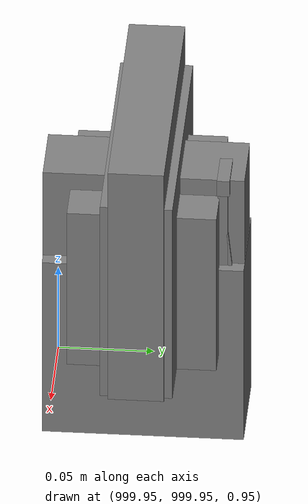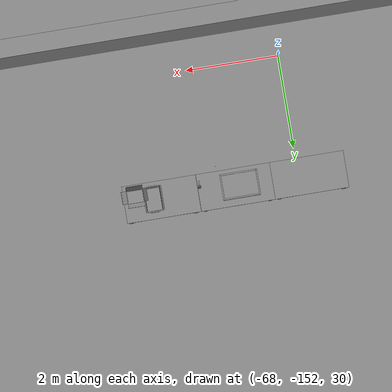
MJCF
<mujoco>
    <option gravity="0.000000000 0.000000000 -9.810000420" timestep="0.0049999999" integrator="implicitfast" density="1.225" viscosity="1.8000001e-05" noslip_iterations="10" iterations="100" sdf_iterations="50">
        <flag multiccd="disable"/>
    </option>
    <size memory="1000M"/>
    <compiler coordinate="local"/>
    <worldbody>
        <light cutoff="30" pos="0 1 1" dir="0 -1 -2"/>
        <light cutoff="30" pos="0 -1 1" dir="0 1 -2"/>
        <body pos="-64.866622925 -149.383972168 30.183746338" euler="89.999984741 89.999946594 0.000000000" name="openloong_gripper_2f85_fix_base_usda_bluebox_01">
            <geom contype="1" conaffinity="1" density="1000" type="box" material="" rgba="0.500000000 0.500000000 0.500000000 1.000000000" solimp="0.899999976 0.949999988 0.001000000" friction="1.000000000 0.005000000 0.000100000" solref="0.020000000 1.000000000" margin="0" condim="3" group="0" pos="0.276580811 0.187225342 0.000068665" quat="0.707106948 0.000077471 0.707106352 0.000077486" size="0.100000001 0.057999998 0.010000000" name="openloong_gripper_2f85_fix_base_usda_geom_7E3204B4_28C1_4839_AC0E_52A6D7057B25"/>
            <geom contype="1" conaffinity="1" density="1000" type="box" material="" rgba="0.500000000 0.500000000 0.500000000 1.000000000" solimp="0.899999976 0.949999988 0.001000000" friction="1.000000000 0.005000000 0.000100000" solref="0.020000000 1.000000000" margin="0" condim="3" group="0" pos="0.000000000 0.002883911 0.000000000" quat="0.999999881 0.000000000 0.000000000 0.000000000" size="0.254000008 0.003000000 0.172000006" name="openloong_gripper_2f85_fix_base_usda_geom_3330A71B_367F_448E_9B41_6E13C5B61D74"/>
            <geom contype="1" conaffinity="1" density="1000" type="box" material="" rgba="0.500000000 0.500000000 0.500000000 1.000000000" solimp="0.899999976 0.949999988 0.001000000" friction="1.000000000 0.005000000 0.000100000" solref="0.020000000 1.000000000" margin="0" condim="3" group="0" pos="0.000000000 0.124874115 0.173484802" quat="0.999796331 0.020176515 -0.000000015 0.000000030" size="0.259999990 0.119999997 0.007000000" name="openloong_gripper_2f85_fix_base_usda_geom_AA4C532E_F478_4618_9E3F_F2EB8AF2733C"/>
            <geom contype="1" conaffinity="1" density="1000" type="box" material="" rgba="0.500000000 0.500000000 0.500000000 1.000000000" solimp="0.899999976 0.949999988 0.001000000" friction="1.000000000 0.005000000 0.000100000" solref="0.020000000 1.000000000" margin="0" condim="3" group="0" pos="0.000000000 0.124874115 -0.173469543" quat="0.999796331 -0.020176545 -0.000000015 0.000000000" size="0.259999990 0.119999997 0.007000000" name="openloong_gripper_2f85_fix_base_usda_geom_BD99E32F_D412_4D4F_9093_D75EA4F73F2E"/>
            <geom contype="1" conaffinity="1" density="1000" type="box" material="" rgba="0.500000000 0.500000000 0.500000000 1.000000000" solimp="0.899999976 0.949999988 0.001000000" friction="1.000000000 0.005000000 0.000100000" solref="0.020000000 1.000000000" margin="0" condim="3" group="0" pos="0.000000000 0.214008331 0.188980103" quat="0.999912977 0.013176724 0.000000015 0.000000000" size="0.259999990 0.029999999 0.012500000" name="openloong_gripper_2f85_fix_base_usda_geom_0E768723_97D3_4678_915C_62EDA952497E"/>
            <geom contype="1" conaffinity="1" density="1000" type="box" material="" rgba="0.500000000 0.500000000 0.500000000 1.000000000" solimp="0.899999976 0.949999988 0.001000000" friction="1.000000000 0.005000000 0.000100000" solref="0.020000000 1.000000000" margin="0" condim="3" group="0" pos="-0.258361816 0.125289917 0.001876831" quat="0.702796936 -0.020792112 0.710783124 0.020769298" size="0.189999998 0.119999997 0.009000000" name="openloong_gripper_2f85_fix_base_usda_geom_18C3FDEF_09F9_4C27_A966_980F7BDE757C"/>
            <geom contype="1" conaffinity="1" density="1000" type="box" material="" rgba="0.500000000 0.500000000 0.500000000 1.000000000" solimp="0.899999976 0.949999988 0.001000000" friction="1.000000000 0.005000000 0.000100000" solref="0.020000000 1.000000000" margin="0" condim="3" group="0" pos="0.000000000 0.214008331 -0.188980103" quat="0.999912977 -0.013176769 0.000000030 0.000000015" size="0.259999990 0.029999999 0.012500000" name="openloong_gripper_2f85_fix_base_usda_geom_2CA9D976_ACDF_4F2A_91D7_F5F322682807"/>
            <geom contype="1" conaffinity="1" density="1000" type="box" material="" rgba="0.500000000 0.500000000 0.500000000 1.000000000" solimp="0.899999976 0.949999988 0.001000000" friction="1.000000000 0.005000000 0.000100000" solref="0.020000000 1.000000000" margin="0" condim="3" group="0" pos="-0.276611328 0.187225342 0.000068665" quat="0.707106650 0.000077441 0.707106709 0.000077456" size="0.100000001 0.057999998 0.010000000" name="openloong_gripper_2f85_fix_base_usda_geom_FC478427_63AD_49B3_B7E2_16105F67B4A7"/>
            <geom contype="1" conaffinity="1" density="1000" type="box" material="" rgba="0.500000000 0.500000000 0.500000000 1.000000000" solimp="0.899999976 0.949999988 0.001000000" friction="1.000000000 0.005000000 0.000100000" solref="0.020000000 1.000000000" margin="0" condim="3" group="0" pos="0.258331299 0.125289917 0.001876831" quat="0.702851415 0.018856421 0.710823774 -0.019329369" size="0.189999998 0.119999997 0.009000000" name="openloong_gripper_2f85_fix_base_usda_geom_85A42556_153E_4934_929D_10911169ABFB"/>
            <freejoint name="openloong_gripper_2f85_fix_base_usda_bluebox_01_joint"/>
            <site size="0.005000000 0.005000000 0.005000000" rgba="0.500000000 0.500000000 0.500000000 1.000000000" pos="0.000000000 0.000000000 0.000000000" quat="0.999961913 0.008726534 0.000000000 0.000000000" group="0" type="sphere" name="openloong_gripper_2f85_fix_base_usda_bluebox_01site"/>
        </body>
        <body pos="-64.496299744 -149.491867065 30.235729218" euler="0.000000000 0.000000000 89.999946594" name="openloong_gripper_2f85_fix_base_usda_cardboardbox_01">
            <geom contype="1" conaffinity="1" density="1000" type="box" material="" rgba="0.500000000 0.500000000 0.500000000 1.000000000" solimp="0.899999976 0.949999988 0.001000000" friction="1.000000000 0.005000000 0.000100000" solref="0.020000000 1.000000000" margin="0" condim="3" group="0" pos="-0.003166199 -0.004086494 0.005052090" quat="1.000000000 0.000000000 0.000000000 0.000000000" size="0.142499998 0.177500010 0.005000000" name="openloong_gripper_2f85_fix_base_usda_geom_FC3F7C94_8296_4BC7_A52B_75C9893D1186"/>
            <geom contype="1" conaffinity="1" density="1000" type="box" material="" rgba="0.500000000 0.500000000 0.500000000 1.000000000" solimp="0.899999976 0.949999988 0.001000000" friction="1.000000000 0.005000000 0.000100000" solref="0.020000000 1.000000000" margin="0" condim="3" group="0" pos="-0.003166199 0.170316696 0.150570869" quat="1.000000000 0.000000000 0.000000000 0.000000000" size="0.142499998 0.005000000 0.149999991" name="openloong_gripper_2f85_fix_base_usda_geom_8EC87CE9_DA07_4BAF_B280_902381EBCB95"/>
            <geom contype="1" conaffinity="1" density="1000" type="box" material="" rgba="0.500000000 0.500000000 0.500000000 1.000000000" solimp="0.899999976 0.949999988 0.001000000" friction="1.000000000 0.005000000 0.000100000" solref="0.020000000 1.000000000" margin="0" condim="3" group="0" pos="-0.147399902 -0.005307198 0.150570869" quat="1.000000000 0.000000000 0.000000000 0.000000000" size="0.005000000 0.177500010 0.149999991" name="openloong_gripper_2f85_fix_base_usda_geom_EC233E48_5055_49D3_A26A_ED9C4DCF2482"/>
            <geom contype="1" conaffinity="1" density="1000" type="box" material="" rgba="0.500000000 0.500000000 0.500000000 1.000000000" solimp="0.899999976 0.949999988 0.001000000" friction="1.000000000 0.005000000 0.000100000" solref="0.020000000 1.000000000" margin="0" condim="3" group="0" pos="0.140275955 -0.005307198 0.150570869" quat="1.000000000 0.000000000 0.000000000 0.000000000" size="0.005000000 0.177500010 0.149999991" name="openloong_gripper_2f85_fix_base_usda_geom_87460626_7E33_40AA_A509_14726B1119B3"/>
            <geom contype="1" conaffinity="1" density="1000" type="box" material="" rgba="0.500000000 0.500000000 0.500000000 1.000000000" solimp="0.899999976 0.949999988 0.001000000" friction="1.000000000 0.005000000 0.000100000" solref="0.020000000 1.000000000" margin="0" condim="3" group="0" pos="-0.003166199 -0.181550980 0.150570869" quat="1.000000000 0.000000000 0.000000000 0.000000000" size="0.142499998 0.005000000 0.149999991" name="openloong_gripper_2f85_fix_base_usda_geom_4FC33A82_CE87_4683_9887_89B5F997E0FF"/>
            <freejoint name="openloong_gripper_2f85_fix_base_usda_cardboardbox_01_joint"/>
            <site size="0.005000000 0.005000000 0.005000000" rgba="0.500000000 0.500000000 0.500000000 1.000000000" pos="0.000000000 0.000000000 0.000000000" quat="0.999961913 0.008726535 0.000000000 0.000000000" group="0" type="sphere" name="openloong_gripper_2f85_fix_base_usda_site_33CF7216_A764_47A9_999E_8322FCD51239"/>
            <body pos="0.139160156 -0.004048347 0.301930904" euler="-179.999954224 49.383502960 179.999954224" name="openloong_gripper_2f85_fix_base_usda_A1_006">
                <geom contype="1" conaffinity="1" density="1000" type="box" material="" rgba="0.500000000 0.500000000 0.500000000 1.000000000" solimp="0.899999976 0.949999988 0.001000000" friction="1.000000000 0.005000000 0.000100000" solref="0.020000000 1.000000000" margin="0" condim="3" group="0" pos="-0.071587563 0.000009537 0.001745224" quat="0.999999881 0.000000000 0.000000000 0.000000000" size="0.071249999 0.179999992 0.002500000" name="openloong_gripper_2f85_fix_base_usda_geom_C61CA8A8_EAE9_439B_AC50_A60DAA956861"/>
                <joint armature="0" stiffness="0.07" damping="0.0099999998" axis="0.000000 1.000000 0.000000" type="hinge" name="openloong_gripper_2f85_fix_base_usda_A1_006"/>
            </body>
            <body pos="-0.145902634 -0.004086494 0.301938057" euler="-180.000000000 -60.000011444 -180.000000000" name="openloong_gripper_2f85_fix_base_usda_A2_006">
                <geom contype="1" conaffinity="1" density="1000" type="box" material="" rgba="0.500000000 0.500000000 0.500000000 1.000000000" solimp="0.899999976 0.949999988 0.001000000" friction="1.000000000 0.005000000 0.000100000" solref="0.020000000 1.000000000" margin="0" condim="3" group="0" pos="0.071268082 0.000009537 0.002717972" quat="0.000002921 0.000000000 -0.000000030 0.999999881" size="0.071249999 0.179999992 0.002500000" name="openloong_gripper_2f85_fix_base_usda_geom_9CA8DCA9_4AF0_450B_9369_DDED5705794A"/>
                <joint armature="0" stiffness="0.07" damping="0.0099999998" axis="0.000000 1.000000 0.000000" type="hinge" name="openloong_gripper_2f85_fix_base_usda_A2_006"/>
            </body>
            <body pos="-0.003385544 0.175991058 0.301930904" euler="-125.858116150 -0.000004561 0.000002331" name="openloong_gripper_2f85_fix_base_usda_B2_006">
                <geom contype="1" conaffinity="1" density="1000" type="box" material="" rgba="0.500000000 0.500000000 0.500000000 1.000000000" solimp="0.899999976 0.949999988 0.001000000" friction="1.000000000 0.005000000 0.000100000" solref="0.020000000 1.000000000" margin="0" condim="3" group="0" pos="0.000009537 -0.070939064 -0.002470016" quat="0.999614120 0.027776197 -0.000000015 0.000000030" size="0.137500003 0.064999998 0.005000000" name="openloong_gripper_2f85_fix_base_usda_geom_334652BC_C954_4B9B_B334_AE3E24CA01E1"/>
                <joint armature="0" stiffness="0.07" damping="0.0099999998" axis="1.000000 0.000000 0.000000" type="hinge" name="openloong_gripper_2f85_fix_base_usda_B2_006"/>
            </body>
            <body pos="-0.003385544 -0.184140205 0.301938057" euler="147.805557251 0.000000000 0.000000000" name="openloong_gripper_2f85_fix_base_usda_B1_006">
                <geom contype="1" conaffinity="1" density="1000" type="box" material="" rgba="0.500000000 0.500000000 0.500000000 1.000000000" solimp="0.899999976 0.949999988 0.001000000" friction="1.000000000 0.005000000 0.000100000" solref="0.020000000 1.000000000" margin="0" condim="3" group="0" pos="-0.000028610 0.070202351 -0.002703667" quat="0.999614179 -0.027776167 0.000000000 0.000000000" size="0.137500003 0.064999998 0.005000000" name="openloong_gripper_2f85_fix_base_usda_geom_F4954712_0E74_4290_9F60_432EE68DEBCF"/>
                <joint armature="0" stiffness="0.07" damping="0.0099999998" axis="1.000000 0.000000 0.000000" type="hinge" name="openloong_gripper_2f85_fix_base_usda_B1_006"/>
            </body>
        </body>
        <body pos="-65.882858276 -149.481979370 30.229999542" euler="-64.487716675 0.000000000 0.000000000" name="openloong_gripper_2f85_fix_base_usda_Barcode">
            <geom contype="1" conaffinity="1" density="1000" type="box" material="" rgba="0.500000000 0.500000000 0.500000000 1.000000000" solimp="0.899999976 0.949999988 0.001000000" friction="1.000000000 0.005000000 0.000100000" solref="0.020000000 1.000000000" margin="0" condim="3" group="0" pos="0.000000000 0.013038635 0.001419067" quat="0.000000000 0.000000000 0.000000000 1.000000119" size="0.034000002 0.010000000 0.017999999" name="openloong_gripper_2f85_fix_base_usda_geom_1B1FB738_0252_4590_AE33_E2B01304C9A7"/>
            <geom contype="1" conaffinity="1" density="1000" type="box" material="" rgba="0.500000000 0.500000000 0.500000000 1.000000000" solimp="0.899999976 0.949999988 0.001000000" friction="1.000000000 0.005000000 0.000100000" solref="0.020000000 1.000000000" margin="0" condim="3" group="0" pos="0.000000000 -0.035301208 -0.007095337" quat="0.000000000 0.000000000 -0.043619365 0.999048233" size="0.028999999 0.010000000 0.020000000" name="openloong_gripper_2f85_fix_base_usda_geom_8078B925_14C6_41D2_959D_90627D441ED0"/>
            <geom contype="1" conaffinity="1" density="1000" type="box" material="" rgba="0.500000000 0.500000000 0.500000000 1.000000000" solimp="0.899999976 0.949999988 0.001000000" friction="1.000000000 0.005000000 0.000100000" solref="0.020000000 1.000000000" margin="0" condim="3" group="0" pos="0.000000000 -0.043411255 -0.011749268" quat="0.922262907 0.386563420 0.000000000 0.000000000" size="0.026000001 0.010000000 0.020000000" name="openloong_gripper_2f85_fix_base_usda_geom_9811C8DC_717B_4024_8DEF_FF98D31832C0"/>
            <geom contype="1" conaffinity="1" density="1000" type="box" material="" rgba="0.500000000 0.500000000 0.500000000 1.000000000" solimp="0.899999976 0.949999988 0.001000000" friction="1.000000000 0.005000000 0.000100000" solref="0.020000000 1.000000000" margin="0" condim="3" group="0" pos="0.000000000 -0.016967773 -0.031860352" quat="0.000000000 0.000000000 0.000000000 1.000000119" size="0.008000000 0.010000000 0.013000000" name="openloong_gripper_2f85_fix_base_usda_geom_6F77BF1A_7E4D_4703_9487_1F715E6B40D7"/>
            <geom contype="1" conaffinity="1" density="1000" type="box" material="" rgba="0.500000000 0.500000000 0.500000000 1.000000000" solimp="0.899999976 0.949999988 0.001000000" friction="1.000000000 0.005000000 0.000100000" solref="0.020000000 1.000000000" margin="0" condim="3" group="0" pos="0.000000000 -0.001869202 0.000312805" quat="0.953716993 0.300705761 0.000000000 0.000000000" size="0.032000002 0.010000000 0.018999999" name="openloong_gripper_2f85_fix_base_usda_geom_8405A73F_236D_4441_8B11_A7E01457CDF5"/>
            <geom contype="1" conaffinity="1" density="1000" type="box" material="" rgba="0.500000000 0.500000000 0.500000000 1.000000000" solimp="0.899999976 0.949999988 0.001000000" friction="1.000000000 0.005000000 0.000100000" solref="0.020000000 1.000000000" margin="0" condim="3" group="0" pos="0.000000000 -0.019531250 -0.003173828" quat="0.953716993 0.300705761 0.000000000 0.000000000" size="0.030999999 0.010000000 0.020000000" name="openloong_gripper_2f85_fix_base_usda_geom_0F0E4BB9_9EC7_4BD9_BE08_02FE164D213B"/>
            <geom contype="1" conaffinity="1" density="1000" type="box" material="" rgba="0.500000000 0.500000000 0.500000000 1.000000000" solimp="0.899999976 0.949999988 0.001000000" friction="1.000000000 0.005000000 0.000100000" solref="0.020000000 1.000000000" margin="0" condim="3" group="0" pos="0.000000000 -0.035301208 -0.007095337" quat="0.953716993 0.300705761 0.000000000 0.000000000" size="0.028999999 0.010000000 0.020000000" name="openloong_gripper_2f85_fix_base_usda_geom_FD8F16DB_2F5F_4A8D_81CF_5D8CA37E397E"/>
            <geom contype="1" conaffinity="1" density="1000" type="box" material="" rgba="0.500000000 0.500000000 0.500000000 1.000000000" solimp="0.899999976 0.949999988 0.001000000" friction="1.000000000 0.005000000 0.000100000" solref="0.020000000 1.000000000" margin="0" condim="3" group="0" pos="0.000000000 -0.042617798 -0.071121216" quat="0.000000000 0.000000000 0.000000000 1.000000119" size="0.013000000 0.021000000 0.059999999" name="openloong_gripper_2f85_fix_base_usda_geom_DB46474B_E9A5_4940_87D9_808D3A8D8EF0"/>
            <freejoint name="openloong_gripper_2f85_fix_base_usda_Barcode_joint"/>
            <site size="0.005000000 0.005000000 0.005000000" rgba="0.500000000 0.500000000 0.500000000 1.000000000" pos="0.000000000 0.000000000 0.000000000" quat="1.000000000 0.000000000 0.000000000 0.000000000" group="0" type="sphere" name="openloong_gripper_2f85_fix_base_usda_Barcode_site"/>
        </body>
        <body pos="-66.745018005 -149.392349243 30.184000015" euler="0.000000000 0.000000000 89.999946594" name="[22331412856352]_Basket_01">
            <geom contype="1" conaffinity="1" density="1000" type="box" material="" rgba="0.500000000 0.500000000 0.500000000 1.000000000" solimp="0.899999976 0.949999988 0.001000000" friction="1.000000000 0.005000000 0.000100000" solref="0.020000000 1.000000000" margin="0" condim="3" group="0" pos="-0.052425385 0.389207840 0.089787483" quat="0.707107008 0.000000000 0.000000000 0.707106411" size="0.014249999 0.014249999 0.059999999" name="[22331412856352]_geom_42F28E9A_E16A_408F_97FE_AC34C82F6903"/>
            <geom contype="1" conaffinity="1" density="1000" type="box" material="" rgba="0.500000000 0.500000000 0.500000000 1.000000000" solimp="0.899999976 0.949999988 0.001000000" friction="1.000000000 0.005000000 0.000100000" solref="0.020000000 1.000000000" margin="0" condim="3" group="0" pos="0.264015198 -0.133043289 0.089787483" quat="0.707107008 0.000000000 0.000000000 0.707106411" size="0.014249999 0.014249999 0.059999999" name="[22331412856352]_geom_058CB55A_0CD2_4512_8061_28668C0F6006"/>
            <geom contype="1" conaffinity="1" density="1000" type="box" material="" rgba="0.500000000 0.500000000 0.500000000 1.000000000" solimp="0.899999976 0.949999988 0.001000000" friction="1.000000000 0.005000000 0.000100000" solref="0.020000000 1.000000000" margin="0" condim="3" group="0" pos="-0.264015198 -0.265548706 0.089793205" quat="0.707107008 0.000000000 0.000000000 0.707106411" size="0.014249999 0.014249999 0.059999999" name="[22331412856352]_geom_CC48B05C_BBD4_42E4_BE01_2D933454D82D"/>
            <geom contype="1" conaffinity="1" density="1000" type="box" material="" rgba="0.500000000 0.500000000 0.500000000 1.000000000" solimp="0.899999976 0.949999988 0.001000000" friction="1.000000000 0.005000000 0.000100000" solref="0.020000000 1.000000000" margin="0" condim="3" group="0" pos="-0.160263062 -0.389322281 0.089793205" quat="0.707107008 0.000000000 0.000000000 0.707106411" size="0.014249999 0.014249999 0.059999999" name="[22331412856352]_geom_B3C98DBF_1DF5_4D51_A813_22705C4EBB80"/>
            <geom contype="1" conaffinity="1" density="1000" type="box" material="" rgba="0.500000000 0.500000000 0.500000000 1.000000000" solimp="0.899999976 0.949999988 0.001000000" friction="1.000000000 0.005000000 0.000100000" solref="0.020000000 1.000000000" margin="0" condim="3" group="0" pos="0.162265778 -0.389322281 0.089787483" quat="0.707107008 0.000000000 0.000000000 0.707106411" size="0.014249999 0.014249999 0.059999999" name="[22331412856352]_geom_5AEE9402_63F1_4EB9_BAD8_0E58219DB081"/>
            <geom contype="1" conaffinity="1" density="1000" type="box" material="" rgba="0.500000000 0.500000000 0.500000000 1.000000000" solimp="0.899999976 0.949999988 0.001000000" friction="1.000000000 0.005000000 0.000100000" solref="0.020000000 1.000000000" margin="0" condim="3" group="0" pos="0.264015198 0.389207840 0.089787483" quat="0.707107008 0.000000000 0.000000000 0.707106411" size="0.014249999 0.014249999 0.059999999" name="[22331412856352]_geom_320E483F_ECC1_4F0D_A181_28373568DF4A"/>
            <geom contype="1" conaffinity="1" density="1000" type="box" material="" rgba="0.500000000 0.500000000 0.500000000 1.000000000" solimp="0.899999976 0.949999988 0.001000000" friction="1.000000000 0.005000000 0.000100000" solref="0.020000000 1.000000000" margin="0" condim="3" group="0" pos="-0.264015198 -0.133043289 0.089793205" quat="0.707107008 0.000000000 0.000000000 0.707106411" size="0.014249999 0.014249999 0.059999999" name="[22331412856352]_geom_A82E6705_EB0A_4CD4_A03C_1B243CC7F4E8"/>
            <geom contype="1" conaffinity="1" density="1000" type="box" material="" rgba="0.500000000 0.500000000 0.500000000 1.000000000" solimp="0.899999976 0.949999988 0.001000000" friction="1.000000000 0.005000000 0.000100000" solref="0.020000000 1.000000000" margin="0" condim="3" group="0" pos="-0.264026642 0.269256592 0.089793205" quat="0.707107008 0.000000000 0.000000000 0.707106411" size="0.014249999 0.014249999 0.059999999" name="[22331412856352]_geom_63737981_AE2B_46E0_AB97_00DBD61A090C"/>
            <geom contype="1" conaffinity="1" density="1000" type="box" material="" rgba="0.500000000 0.500000000 0.500000000 1.000000000" solimp="0.899999976 0.949999988 0.001000000" friction="1.000000000 0.005000000 0.000100000" solref="0.020000000 1.000000000" margin="0" condim="3" group="0" pos="0.054462433 0.389207840 0.089787483" quat="0.707107008 0.000000000 0.000000000 0.707106411" size="0.014249999 0.014249999 0.059999999" name="[22331412856352]_geom_639EEC49_671B_4694_8B6C_81F9DA56CFA9"/>
            <geom contype="1" conaffinity="1" density="1000" type="box" material="" rgba="0.500000000 0.500000000 0.500000000 1.000000000" solimp="0.899999976 0.949999988 0.001000000" friction="1.000000000 0.005000000 0.000100000" solref="0.020000000 1.000000000" margin="0" condim="3" group="0" pos="0.054462433 -0.389322281 0.089787483" quat="0.707107008 0.000000000 0.000000000 0.707106411" size="0.014249999 0.014249999 0.059999999" name="[22331412856352]_geom_7BAA2146_1320_46F4_AA0B_ABC3F5D348C3"/>
            <geom contype="1" conaffinity="1" density="1000" type="box" material="" rgba="0.500000000 0.500000000 0.500000000 1.000000000" solimp="0.899999976 0.949999988 0.001000000" friction="1.000000000 0.005000000 0.000100000" solref="0.020000000 1.000000000" margin="0" condim="3" group="0" pos="0.264015198 0.269256592 0.089793205" quat="0.707107008 0.000000000 0.000000000 0.707106411" size="0.014249999 0.014249999 0.059999999" name="[22331412856352]_geom_5C06037A_5D2D_42B2_8A14_9DDC3AA8991A"/>
            <geom contype="1" conaffinity="1" density="1000" type="box" material="" rgba="0.500000000 0.500000000 0.500000000 1.000000000" solimp="0.899999976 0.949999988 0.001000000" friction="1.000000000 0.005000000 0.000100000" solref="0.020000000 1.000000000" margin="0" condim="3" group="0" pos="0.264015198 -0.389322281 0.089787483" quat="0.707107008 0.000000000 0.000000000 0.707106411" size="0.014249999 0.014249999 0.059999999" name="[22331412856352]_geom_033726CD_BE69_4CFE_98D1_5BB4957DCC17"/>
            <geom contype="1" conaffinity="1" density="1000" type="box" material="" rgba="0.500000000 0.500000000 0.500000000 1.000000000" solimp="0.899999976 0.949999988 0.001000000" friction="1.000000000 0.005000000 0.000100000" solref="0.020000000 1.000000000" margin="0" condim="3" group="0" pos="0.000000000 0.000000000 0.015998840" quat="0.707107008 0.000000000 0.000000000 0.707106411" size="0.403499991 0.279000014 0.015750000" name="[22331412856352]_geom_85EA1336_7F52_4D4A_97E3_A9FA2D272A5A"/>
            <geom contype="1" conaffinity="1" density="1000" type="box" material="" rgba="0.500000000 0.500000000 0.500000000 1.000000000" solimp="0.899999976 0.949999988 0.001000000" friction="1.000000000 0.005000000 0.000100000" solref="0.020000000 1.000000000" margin="0" condim="3" group="0" pos="0.000000000 -0.389476776 0.163619041" quat="0.707107008 0.000000000 0.000000000 0.707106411" size="0.015000000 0.277500004 0.015750000" name="[22331412856352]_geom_B28A44CF_356E_4D8F_AF7F_0423273EDDB4"/>
            <geom contype="1" conaffinity="1" density="1000" type="box" material="" rgba="0.500000000 0.500000000 0.500000000 1.000000000" solimp="0.899999976 0.949999988 0.001000000" friction="1.000000000 0.005000000 0.000100000" solref="0.020000000 1.000000000" margin="0" condim="3" group="0" pos="0.162265778 0.389207840 0.089787483" quat="0.707107008 0.000000000 0.000000000 0.707106411" size="0.014249999 0.014249999 0.059999999" name="[22331412856352]_geom_758C9CC1_A3FF_4619_8FBF_DEC35C857BC9"/>
            <geom contype="1" conaffinity="1" density="1000" type="box" material="" rgba="0.500000000 0.500000000 0.500000000 1.000000000" solimp="0.899999976 0.949999988 0.001000000" friction="1.000000000 0.005000000 0.000100000" solref="0.020000000 1.000000000" margin="0" condim="3" group="0" pos="0.000000000 0.389471054 0.163619041" quat="0.707107008 0.000000000 0.000000000 0.707106411" size="0.015000000 0.277500004 0.015750000" name="[22331412856352]_geom_5A82D19E_4151_489B_85C2_8DB2EF8FDC38"/>
            <geom contype="1" conaffinity="1" density="1000" type="box" material="" rgba="0.500000000 0.500000000 0.500000000 1.000000000" solimp="0.899999976 0.949999988 0.001000000" friction="1.000000000 0.005000000 0.000100000" solref="0.020000000 1.000000000" margin="0" condim="3" group="0" pos="-0.263511658 0.000000000 0.163619041" quat="0.707107008 0.000000000 0.000000000 0.707106411" size="0.403499991 0.015000000 0.015750000" name="[22331412856352]_geom_3A58EBB3_6937_479B_B08D_0FBC17CFCC70"/>
            <geom contype="1" conaffinity="1" density="1000" type="box" material="" rgba="0.500000000 0.500000000 0.500000000 1.000000000" solimp="0.899999976 0.949999988 0.001000000" friction="1.000000000 0.005000000 0.000100000" solref="0.020000000 1.000000000" margin="0" condim="3" group="0" pos="-0.264015198 0.141334534 0.089793205" quat="0.707107008 0.000000000 0.000000000 0.707106411" size="0.014249999 0.014249999 0.059999999" name="[22331412856352]_geom_EDAACA58_44F1_4C2E_98A9_A00F3789108D"/>
            <geom contype="1" conaffinity="1" density="1000" type="box" material="" rgba="0.500000000 0.500000000 0.500000000 1.000000000" solimp="0.899999976 0.949999988 0.001000000" friction="1.000000000 0.005000000 0.000100000" solref="0.020000000 1.000000000" margin="0" condim="3" group="0" pos="0.264015198 -0.265548706 0.089787483" quat="0.707107008 0.000000000 0.000000000 0.707106411" size="0.014249999 0.014249999 0.059999999" name="[22331412856352]_geom_CE067A19_FFF1_4219_AFB8_556F3E9766AC"/>
            <geom contype="1" conaffinity="1" density="1000" type="box" material="" rgba="0.500000000 0.500000000 0.500000000 1.000000000" solimp="0.899999976 0.949999988 0.001000000" friction="1.000000000 0.005000000 0.000100000" solref="0.020000000 1.000000000" margin="0" condim="3" group="0" pos="-0.160263062 0.389207840 0.089787483" quat="0.707107008 0.000000000 0.000000000 0.707106411" size="0.014249999 0.014249999 0.059999999" name="[22331412856352]_geom_6199188B_E3C9_4F44_AE70_18B2FF199168"/>
            <geom contype="1" conaffinity="1" density="1000" type="box" material="" rgba="0.500000000 0.500000000 0.500000000 1.000000000" solimp="0.899999976 0.949999988 0.001000000" friction="1.000000000 0.005000000 0.000100000" solref="0.020000000 1.000000000" margin="0" condim="3" group="0" pos="-0.052425385 -0.389322281 0.089787483" quat="0.707107008 0.000000000 0.000000000 0.707106411" size="0.014249999 0.014249999 0.059999999" name="[22331412856352]_geom_4BE6FEC4_3AB7_4355_B163_F99E4E1EC1B1"/>
            <geom contype="1" conaffinity="1" density="1000" type="box" material="" rgba="0.500000000 0.500000000 0.500000000 1.000000000" solimp="0.899999976 0.949999988 0.001000000" friction="1.000000000 0.005000000 0.000100000" solref="0.020000000 1.000000000" margin="0" condim="3" group="0" pos="-0.264026642 -0.389322281 0.089793205" quat="0.707107008 0.000000000 0.000000000 0.707106411" size="0.014249999 0.014249999 0.059999999" name="[22331412856352]_geom_78315EBC_7F04_4684_B2C1_9A0D683C23C2"/>
            <geom contype="1" conaffinity="1" density="1000" type="box" material="" rgba="0.500000000 0.500000000 0.500000000 1.000000000" solimp="0.899999976 0.949999988 0.001000000" friction="1.000000000 0.005000000 0.000100000" solref="0.020000000 1.000000000" margin="0" condim="3" group="0" pos="0.264015198 0.141334534 0.089787483" quat="0.707107008 0.000000000 0.000000000 0.707106411" size="0.014249999 0.014249999 0.059999999" name="[22331412856352]_geom_30EBE96B_78F8_4B1C_9298_29F2D7CE57BF"/>
            <geom contype="1" conaffinity="1" density="1000" type="box" material="" rgba="0.500000000 0.500000000 0.500000000 1.000000000" solimp="0.899999976 0.949999988 0.001000000" friction="1.000000000 0.005000000 0.000100000" solref="0.020000000 1.000000000" margin="0" condim="3" group="0" pos="-0.264015198 0.389207840 0.089793205" quat="0.707107008 0.000000000 0.000000000 0.707106411" size="0.014249999 0.014249999 0.059999999" name="[22331412856352]_geom_384392F4_FB97_4C4A_AF8E_61FEA96B167C"/>
            <geom contype="1" conaffinity="1" density="1000" type="box" material="" rgba="0.500000000 0.500000000 0.500000000 1.000000000" solimp="0.899999976 0.949999988 0.001000000" friction="1.000000000 0.005000000 0.000100000" solref="0.020000000 1.000000000" margin="0" condim="3" group="0" pos="0.264015198 0.004480362 0.089787483" quat="0.707107008 0.000000000 0.000000000 0.707106411" size="0.014249999 0.014249999 0.059999999" name="[22331412856352]_geom_1648DDEF_F74E_49B5_8383_83A7D8A41A42"/>
            <geom contype="1" conaffinity="1" density="1000" type="box" material="" rgba="0.500000000 0.500000000 0.500000000 1.000000000" solimp="0.899999976 0.949999988 0.001000000" friction="1.000000000 0.005000000 0.000100000" solref="0.020000000 1.000000000" margin="0" condim="3" group="0" pos="0.263694763 -0.000011444 0.163619041" quat="0.707107008 0.000000000 0.000000000 0.707106411" size="0.403499991 0.015000000 0.015750000" name="[22331412856352]_geom_EAC74F09_66DA_43FE_B26B_89B51EB9CB51"/>
            <geom contype="1" conaffinity="1" density="1000" type="box" material="" rgba="0.500000000 0.500000000 0.500000000 1.000000000" solimp="0.899999976 0.949999988 0.001000000" friction="1.000000000 0.005000000 0.000100000" solref="0.020000000 1.000000000" margin="0" condim="3" group="0" pos="-0.264015198 0.004480362 0.089793205" quat="0.707107008 0.000000000 0.000000000 0.707106411" size="0.014249999 0.014249999 0.059999999" name="[22331412856352]_geom_EDE78498_6347_4FD0_AD2B_BBF83A9B12E5"/>
            <freejoint name="[22331412856352]_joint_CD4527D2_BC76_4E97_85F8_E157C81F3CBD"/>
        </body>
        <body pos="0.000000000 0.000000000 0.000000000" euler="0.000000000 0.000000000 0.000000000" name="Static Objects_Static Objects">
            <geom contype="1" conaffinity="1" density="1000" type="box" material="" rgba="0.500000000 0.500000000 0.500000000 1.000000000" solimp="0.899999976 0.949999988 0.001000000" friction="1.000000000 0.005000000 0.000100000" solref="0.020000000 1.000000000" margin="0" condim="3" group="0" pos="-67.544113159 -149.365814209 29.727830887" quat="0.500000417 0.499999970 0.499999553 0.499999970" size="0.381000012 0.319999993 0.041000001" name="Static Objects_geom_D3ECA8F7_922F_46C9_B3AF_BE3A5F77F1A5"/>
            <geom contype="1" conaffinity="1" density="1000" type="box" material="" rgba="0.500000000 0.500000000 0.500000000 1.000000000" solimp="0.899999976 0.949999988 0.001000000" friction="1.000000000 0.005000000 0.000100000" solref="0.020000000 1.000000000" margin="0" condim="3" group="0" pos="-68.239501953 -149.365814209 30.086868286" quat="0.500000417 0.499999970 0.499999553 0.499999970" size="0.370999992 0.039500002 0.745000005" name="Static Objects_geom_8064E406_2C66_4A42_94F4_BB2A4348F5E2"/>
            <geom contype="1" conaffinity="1" density="1000" type="box" material="" rgba="0.500000000 0.500000000 0.500000000 1.000000000" solimp="0.899999976 0.949999988 0.001000000" friction="1.000000000 0.005000000 0.000100000" solref="0.020000000 1.000000000" margin="0" condim="3" group="0" pos="-68.239501953 -149.365814209 30.147235870" quat="0.500000417 0.499999970 0.499999553 0.499999970" size="0.400000006 0.022000000 0.800000012" name="Static Objects_geom_1C182D2B_FA1E_4641_A4DD_D421ADF2A680"/>
            <geom contype="1" conaffinity="1" density="1000" type="box" material="" rgba="0.500000000 0.500000000 0.500000000 1.000000000" solimp="0.899999976 0.949999988 0.001000000" friction="1.000000000 0.005000000 0.000100000" solref="0.020000000 1.000000000" margin="0" condim="3" group="0" pos="-68.934890747 -149.365814209 29.727830887" quat="0.500000417 0.499999970 0.499999553 0.499999970" size="0.381000012 0.319999993 0.041000001" name="Static Objects_geom_B02C7819_A479_46C2_83F4_C0D52E123D9E"/>
            <geom contype="1" conaffinity="1" density="1000" type="box" material="" rgba="0.500000000 0.500000000 0.500000000 1.000000000" solimp="0.899999976 0.949999988 0.001000000" friction="1.000000000 0.005000000 0.000100000" solref="0.020000000 1.000000000" margin="0" condim="3" group="0" pos="-68.239501953 -149.365814209 29.561563492" quat="0.500000417 0.499999970 0.499999553 0.499999970" size="0.020000000 0.022000000 0.660000026" name="Static Objects_geom_431759F7_BF73_43A3_A993_FADCAE41CF3C"/>
            <geom contype="1" conaffinity="1" density="1000" type="box" material="" rgba="0.500000000 0.500000000 0.500000000 1.000000000" solimp="0.899999976 0.949999988 0.001000000" friction="1.000000000 0.005000000 0.000100000" solref="0.020000000 1.000000000" margin="0" condim="3" group="0" pos="-65.945671082 -149.365814209 29.727830887" quat="0.500000417 0.499999970 0.499999553 0.499999970" size="0.381000012 0.319999993 0.041000001" name="Static Objects_geom_92D6B173_8318_4EEE_BD84_BE222A48A91F"/>
            <geom contype="1" conaffinity="1" density="1000" type="box" material="" rgba="0.500000000 0.500000000 0.500000000 1.000000000" solimp="0.899999976 0.949999988 0.001000000" friction="1.000000000 0.005000000 0.000100000" solref="0.020000000 1.000000000" margin="0" condim="3" group="0" pos="-66.641059875 -149.365814209 30.086868286" quat="0.500000417 0.499999970 0.499999553 0.499999970" size="0.370999992 0.039500002 0.745000005" name="Static Objects_geom_70F814BB_6796_4020_BE6E_A72EA7E31EF5"/>
            <geom contype="1" conaffinity="1" density="1000" type="box" material="" rgba="0.500000000 0.500000000 0.500000000 1.000000000" solimp="0.899999976 0.949999988 0.001000000" friction="1.000000000 0.005000000 0.000100000" solref="0.020000000 1.000000000" margin="0" condim="3" group="0" pos="-66.641059875 -149.365814209 30.147235870" quat="0.500000417 0.499999970 0.499999553 0.499999970" size="0.400000006 0.022000000 0.800000012" name="Static Objects_geom_6F8B13F2_C85B_403F_9B73_89BDB06753A0"/>
            <geom contype="1" conaffinity="1" density="1000" type="box" material="" rgba="0.500000000 0.500000000 0.500000000 1.000000000" solimp="0.899999976 0.949999988 0.001000000" friction="1.000000000 0.005000000 0.000100000" solref="0.020000000 1.000000000" margin="0" condim="3" group="0" pos="-67.336448669 -149.365814209 29.727830887" quat="0.500000417 0.499999970 0.499999553 0.499999970" size="0.381000012 0.319999993 0.041000001" name="Static Objects_geom_AEC581D4_B125_4909_8E39_6B7021F00F01"/>
            <geom contype="1" conaffinity="1" density="1000" type="box" material="" rgba="0.500000000 0.500000000 0.500000000 1.000000000" solimp="0.899999976 0.949999988 0.001000000" friction="1.000000000 0.005000000 0.000100000" solref="0.020000000 1.000000000" margin="0" condim="3" group="0" pos="-66.641059875 -149.365814209 29.561563492" quat="0.500000417 0.499999970 0.499999553 0.499999970" size="0.020000000 0.022000000 0.660000026" name="Static Objects_geom_E5CBA9C2_E64B_46BB_9FD8_EC829D74B71C"/>
            <geom contype="1" conaffinity="1" density="1000" type="box" material="" rgba="0.500000000 0.500000000 0.500000000 1.000000000" solimp="0.899999976 0.949999988 0.001000000" friction="1.000000000 0.005000000 0.000100000" solref="0.020000000 1.000000000" margin="0" condim="3" group="0" pos="-64.338577271 -149.365814209 29.727830887" quat="0.500000417 0.499999970 0.499999553 0.499999970" size="0.381000012 0.319999993 0.041000001" name="Static Objects_geom_8DD72C27_1835_4912_B0BB_291E8B9F8D13"/>
            <geom contype="1" conaffinity="1" density="1000" type="box" material="" rgba="0.500000000 0.500000000 0.500000000 1.000000000" solimp="0.899999976 0.949999988 0.001000000" friction="1.000000000 0.005000000 0.000100000" solref="0.020000000 1.000000000" margin="0" condim="3" group="0" pos="-65.033966064 -149.365814209 30.086868286" quat="0.500000417 0.499999970 0.499999553 0.499999970" size="0.370999992 0.039500002 0.745000005" name="Static Objects_geom_498EFBFE_DAF5_4643_BC1F_169393CB7A8E"/>
            <geom contype="1" conaffinity="1" density="1000" type="box" material="" rgba="0.500000000 0.500000000 0.500000000 1.000000000" solimp="0.899999976 0.949999988 0.001000000" friction="1.000000000 0.005000000 0.000100000" solref="0.020000000 1.000000000" margin="0" condim="3" group="0" pos="-65.033966064 -149.365814209 30.147235870" quat="0.500000417 0.499999970 0.499999553 0.499999970" size="0.400000006 0.022000000 0.800000012" name="Static Objects_geom_9DDE85C6_9D1B_41F6_90D8_63A37B8E4451"/>
            <geom contype="1" conaffinity="1" density="1000" type="box" material="" rgba="0.500000000 0.500000000 0.500000000 1.000000000" solimp="0.899999976 0.949999988 0.001000000" friction="1.000000000 0.005000000 0.000100000" solref="0.020000000 1.000000000" margin="0" condim="3" group="0" pos="-65.729354858 -149.365814209 29.727830887" quat="0.500000417 0.499999970 0.499999553 0.499999970" size="0.381000012 0.319999993 0.041000001" name="Static Objects_geom_9B549EA9_2CE8_496A_A1B9_AF8BC9576156"/>
            <geom contype="1" conaffinity="1" density="1000" type="box" material="" rgba="0.500000000 0.500000000 0.500000000 1.000000000" solimp="0.899999976 0.949999988 0.001000000" friction="1.000000000 0.005000000 0.000100000" solref="0.020000000 1.000000000" margin="0" condim="3" group="0" pos="-65.033966064 -149.365814209 29.561563492" quat="0.500000417 0.499999970 0.499999553 0.499999970" size="0.020000000 0.022000000 0.660000026" name="Static Objects_geom_30687AF4_E866_42E1_B31C_C02DC9CB7291"/>
            <geom contype="1" conaffinity="1" density="1000" type="box" material="" rgba="0.500000000 0.500000000 0.500000000 1.000000000" solimp="0.899999976 0.949999988 0.001000000" friction="1.000000000 0.005000000 0.000100000" solref="0.020000000 1.000000000" margin="0" condim="3" group="0" pos="-61.754566193 -137.853729248 33.906845093" quat="0.707107067 0.000000000 0.000000000 0.707106471" size="0.759999990 0.759999990 4.500000000" name="Static Objects_geom_2AA77092_456A_497B_AF74_856176AC2875"/>
            <geom contype="1" conaffinity="1" density="1000" type="box" material="" rgba="0.500000000 0.500000000 0.500000000 1.000000000" solimp="0.899999976 0.949999988 0.001000000" friction="1.000000000 0.005000000 0.000100000" solref="0.020000000 1.000000000" margin="0" condim="3" group="0" pos="-57.511135101 -144.927108765 31.707921982" quat="1.000000000 0.000000000 0.000000000 0.000000000" size="0.200000003 8.000000000 2.299999952" name="Static Objects_geom_896C925A_3274_4022_80A4_01CC9EC006FD"/>
            <geom contype="1" conaffinity="1" density="1000" type="box" material="" rgba="0.500000000 0.500000000 0.500000000 1.000000000" solimp="0.899999976 0.949999988 0.001000000" friction="1.000000000 0.005000000 0.000100000" solref="0.020000000 1.000000000" margin="0" condim="3" group="0" pos="-80.517646790 -157.574050903 31.688196182" quat="0.707107067 0.000000000 0.000000000 0.707106471" size="0.600000024 0.600000024 2.299999952" name="Static Objects_geom_59795864_F27F_41D8_B05B_2EC1253C204A"/>
            <geom contype="1" conaffinity="1" density="1000" type="box" material="" rgba="0.500000000 0.500000000 0.500000000 1.000000000" solimp="0.899999976 0.949999988 0.001000000" friction="1.000000000 0.005000000 0.000100000" solref="0.020000000 1.000000000" margin="0" condim="3" group="0" pos="-80.711044312 -147.414932251 31.666158676" quat="1.000000000 0.000000000 0.000000000 0.000000000" size="0.200000003 10.000000000 2.299999952" name="Static Objects_geom_491A9F77_AF15_410E_8154_04FF086B9E6E"/>
            <geom contype="1" conaffinity="1" density="1000" type="box" material="" rgba="0.500000000 0.500000000 0.500000000 1.000000000" solimp="0.899999976 0.949999988 0.001000000" friction="1.000000000 0.005000000 0.000100000" solref="0.020000000 1.000000000" margin="0" condim="3" group="0" pos="-57.687217712 -137.434692383 31.688196182" quat="0.707107067 0.000000000 0.000000000 0.707106471" size="0.600000024 0.600000024 2.299999952" name="Static Objects_geom_F1DF430F_918A_49E9_9039_3CA2738F2CED"/>
            <geom contype="1" conaffinity="1" density="1000" type="box" material="" rgba="0.500000000 0.500000000 0.500000000 1.000000000" solimp="0.899999976 0.949999988 0.001000000" friction="1.000000000 0.005000000 0.000100000" solref="0.020000000 1.000000000" margin="0" condim="3" group="0" pos="-69.537033081 -140.263229370 31.714921951" quat="0.707107067 0.000000000 0.000000000 0.707106471" size="0.759999990 4.500000000 2.299999952" name="Static Objects_geom_C0FBD418_5DC0_4085_A596_EE00DB05AFC7"/>
            <geom contype="1" conaffinity="1" density="1000" type="box" material="" rgba="0.500000000 0.500000000 0.500000000 1.000000000" solimp="0.899999976 0.949999988 0.001000000" friction="1.000000000 0.005000000 0.000100000" solref="0.020000000 1.000000000" margin="0" condim="3" group="0" pos="-80.073638916 -137.853713989 33.906845093" quat="0.707107067 0.000000000 0.000000000 0.707106471" size="0.759999990 0.759999990 4.500000000" name="Static Objects_geom_1B37DDC0_CACA_4C8A_B876_738051B7FFF4"/>
            <geom contype="1" conaffinity="1" density="1000" type="box" material="" rgba="0.500000000 0.500000000 0.500000000 1.000000000" solimp="0.899999976 0.949999988 0.001000000" friction="1.000000000 0.005000000 0.000100000" solref="0.020000000 1.000000000" margin="0" condim="3" group="0" pos="-73.406707764 -155.734664917 31.707921982" quat="1.000000000 0.000000000 0.000000000 0.000000000" size="0.200000003 3.000000000 2.299999952" name="Static Objects_geom_54AEAAB1_75A3_4E52_963A_C735CB9DB8C0"/>
            <geom contype="1" conaffinity="1" density="1000" type="box" material="" rgba="0.500000000 0.500000000 0.500000000 1.000000000" solimp="0.899999976 0.949999988 0.001000000" friction="1.000000000 0.005000000 0.000100000" solref="0.020000000 1.000000000" margin="0" condim="3" group="0" pos="-68.497543335 -137.448257446 31.707921982" quat="0.707107067 0.000000000 0.000000000 0.707106471" size="0.200000003 14.000000000 2.299999952" name="Static Objects_geom_4DFB8BA0_57F8_4B91_BC47_C0F1BD8C513B"/>
            <geom contype="1" conaffinity="1" density="1000" type="cylinder" material="" rgba="0.500000000 0.500000000 0.500000000 1.000000000" solimp="0.899999976 0.949999988 0.001000000" friction="1.000000000 0.005000000 0.000100000" solref="0.020000000 1.000000000" margin="0" condim="3" group="0" pos="-68.868522644 -142.134506226 31.711090088" quat="0.707107067 0.000000000 0.000000000 0.707106471" size="0.509999990 2.299999952 1.000000000" name="Static Objects_geom_295CEDE7_8301_474F_A289_3DE5198D3939"/>
            <geom contype="1" conaffinity="1" density="1000" type="plane" material="" rgba="0.500000000 0.500000000 0.500000000 1.000000000" solimp="0.899999976 0.949999988 0.001000000" friction="1.000000000 0.005000000 0.000100000" solref="0.020000000 1.000000000" margin="0" condim="3" group="0" pos="-72.873703003 -147.131927490 29.409669876" quat="1.000000000 0.000000000 0.000000000 0.000000000" size="18.000000000 14.000000000 1.000000000" name="Static Objects_geom_F57CE143_C1CC_4FEF_A786_D04F5E335AC2"/>
            <geom contype="1" conaffinity="1" density="1000" type="box" material="" rgba="0.500000000 0.500000000 0.500000000 1.000000000" solimp="0.899999976 0.949999988 0.001000000" friction="1.000000000 0.005000000 0.000100000" solref="0.020000000 1.000000000" margin="0" condim="3" group="0" pos="-79.943580627 -157.782272339 31.707921982" quat="0.707107067 0.000000000 0.000000000 0.707106471" size="0.200000003 7.000000000 2.299999952" name="Static Objects_geom_E9FF795F_4FB4_42B4_88A4_FC45304E5E67"/>
            <geom contype="1" conaffinity="1" density="1000" type="box" material="" rgba="0.500000000 0.500000000 0.500000000 1.000000000" solimp="0.899999976 0.949999988 0.001000000" friction="1.000000000 0.005000000 0.000100000" solref="0.020000000 1.000000000" margin="0" condim="3" group="0" pos="-65.421028137 -152.903442383 31.707921982" quat="0.707107067 0.000000000 0.000000000 0.707106471" size="0.200000003 7.800000191 2.299999952" name="Static Objects_geom_A0919927_E77A_4834_B8B8_66B7EF97754E"/>
            <geom contype="1" conaffinity="1" density="1000" type="box" material="" rgba="0.500000000 0.500000000 0.500000000 1.000000000" solimp="0.899999976 0.949999988 0.001000000" friction="1.000000000 0.005000000 0.000100000" solref="0.020000000 1.000000000" margin="0" condim="3" group="0" pos="-74.776908875 -149.964416504 31.688196182" quat="1.000000000 0.000000000 0.000000000 0.000000000" size="0.600000024 0.409999996 2.299999952" name="Static Objects_geom_8A7E6EA7_2821_4491_980A_E21A1E499298"/>
            <geom contype="1" conaffinity="1" density="1000" type="cylinder" material="" rgba="0.500000000 0.500000000 0.500000000 1.000000000" solimp="0.899999976 0.949999988 0.001000000" friction="1.000000000 0.005000000 0.000100000" solref="0.020000000 1.000000000" margin="0" condim="3" group="0" pos="-60.161884308 -142.134506226 31.711090088" quat="0.707107067 0.000000000 0.000000000 0.707106471" size="0.509999990 2.299999952 1.000000000" name="Static Objects_geom_50C3D9E3_AB3A_42F1_9885_177F961F4BFC"/>
            <geom contype="1" conaffinity="1" density="1000" type="cylinder" material="" rgba="0.500000000 0.500000000 0.500000000 1.000000000" solimp="0.899999976 0.949999988 0.001000000" friction="1.000000000 0.005000000 0.000100000" solref="0.020000000 1.000000000" margin="0" condim="3" group="0" pos="-75.382453918 -149.963455200 31.711090088" quat="0.707107067 0.000000000 0.000000000 0.707106471" size="0.409999996 2.299999952 1.000000000" name="Static Objects_geom_76AB5814_4985_4836_A3F0_826946A0BA5F"/>
            <geom contype="1" conaffinity="1" density="1000" type="cylinder" material="" rgba="0.500000000 0.500000000 0.500000000 1.000000000" solimp="0.899999976 0.949999988 0.001000000" friction="1.000000000 0.005000000 0.000100000" solref="0.020000000 1.000000000" margin="0" condim="3" group="0" pos="-74.154960632 -149.963455200 31.711090088" quat="0.707107067 0.000000000 0.000000000 0.707106471" size="0.409999996 2.299999952 1.000000000" name="Static Objects_geom_AC59F782_B9CB_4623_8F25_53160A9DA693"/>
            <geom contype="1" conaffinity="1" density="1000" type="cylinder" material="" rgba="0.500000000 0.500000000 0.500000000 1.000000000" solimp="0.899999976 0.949999988 0.001000000" friction="1.000000000 0.005000000 0.000100000" solref="0.020000000 1.000000000" margin="0" condim="3" group="0" pos="-77.566612244 -142.134506226 31.711090088" quat="0.707107067 0.000000000 0.000000000 0.707106471" size="0.509999990 2.299999952 1.000000000" name="Static Objects_geom_79DC75F1_5DF0_440B_98C4_D5A6E29D5616"/>
        </body>
        <body pos="-65.914291382 -149.255737305 31.167480469" euler="-139.675018311 24.758935928 -110.654022217" mocap="true" name="spotlight4_SpotLight"/>
        <body pos="1000.000000000 1000.000000000 1.000000000" euler="0.000000000 0.000000000 180.000000000" name="openloong_gripper_2f85_fix_base_usda_battery_01">
            <geom contype="1" conaffinity="1" density="1000" type="box" material="" rgba="0.500000000 0.500000000 0.500000000 1.000000000" solimp="0.899999976 0.949999988 0.001000000" friction="1.000000000 0.005000000 0.000100000" solref="0.020000000 1.000000000" margin="0" condim="3" group="0" pos="-0.011123657 -0.041940309 0.101691343" quat="1.000000000 0.000000000 0.000000000 0.000000000" size="0.010800000 0.003375000 0.004725000" name="openloong_gripper_2f85_fix_base_usda_geom_28DC99C7_1D61_4B35_8612_52B0C029F2A8"/>
            <geom contype="1" conaffinity="1" density="1000" type="box" material="" rgba="0.500000000 0.500000000 0.500000000 1.000000000" solimp="0.899999976 0.949999988 0.001000000" friction="1.000000000 0.005000000 0.000100000" solref="0.020000000 1.000000000" margin="0" condim="3" group="0" pos="-0.010876465 -0.044247437 0.047066893" quat="0.998702705 -0.050920475 0.000000000 0.000000000" size="0.009450001 0.002700000 0.024975000" name="openloong_gripper_2f85_fix_base_usda_geom_A31B40A3_723D_4B8D_894A_A367F5177E68"/>
            <geom contype="1" conaffinity="1" density="1000" type="box" material="" rgba="0.500000000 0.500000000 0.500000000 1.000000000" solimp="0.899999976 0.949999988 0.001000000" friction="1.000000000 0.005000000 0.000100000" solref="0.020000000 1.000000000" margin="0" condim="3" group="0" pos="-0.001235962 -0.000659180 0.047381196" quat="1.000000000 0.000000000 0.000000000 0.000000000" size="0.039420001 0.039150000 0.047250003" name="openloong_gripper_2f85_fix_base_usda_geom_2CCA3156_40ED_4B39_874A_E397EDAA46A4"/>
            <geom contype="1" conaffinity="1" density="1000" type="box" material="" rgba="0.500000000 0.500000000 0.500000000 1.000000000" solimp="0.899999976 0.949999988 0.001000000" friction="1.000000000 0.005000000 0.000100000" solref="0.020000000 1.000000000" margin="0" condim="3" group="0" pos="-0.010876465 -0.039138794 0.009851727" quat="1.000000000 0.000000000 0.000000000 0.000000000" size="0.009450001 0.010800000 0.013500000" name="openloong_gripper_2f85_fix_base_usda_geom_E666BA43_9DFC_4A92_8E90_49C433DA85AC"/>
            <geom contype="1" conaffinity="1" density="1000" type="box" material="" rgba="0.500000000 0.500000000 0.500000000 1.000000000" solimp="0.899999976 0.949999988 0.001000000" friction="1.000000000 0.005000000 0.000100000" solref="0.020000000 1.000000000" margin="0" condim="3" group="0" pos="-0.010876465 -0.041528322 0.071508206" quat="1.000000000 0.000000000 0.000000000 0.000000000" size="0.009450001 0.002700000 0.027000001" name="openloong_gripper_2f85_fix_base_usda_geom_7A6D7595_F78B_43B5_BD19_38CF2EE28F5B"/>
            <freejoint name="openloong_gripper_2f85_fix_base_usda_battery_01_joint"/>
            <site size="0.005000000 0.005000000 0.005000000" rgba="0.500000000 0.500000000 0.500000000 1.000000000" pos="0.000000000 0.000000000 0.000000000" quat="0.999961913 0.008726500 0.000000000 0.000000000" group="0" type="sphere" name="openloong_gripper_2f85_fix_base_usda_battery_01site"/>
        </body>
        <body pos="1000.000000000 1000.000000000 1.000000000" euler="0.000000000 0.000000000 180.000000000" name="openloong_gripper_2f85_fix_base_usda_cpu_fan">
            <geom contype="1" conaffinity="1" density="1000" type="box" material="" rgba="0.500000000 0.500000000 0.500000000 1.000000000" solimp="0.899999976 0.949999988 0.001000000" friction="1.000000000 0.005000000 0.000100000" solref="0.020000000 1.000000000" margin="0" condim="3" group="0" pos="0.000000000 0.000000000 0.070034981" quat="0.000000000 0.000000000 0.000000000 1.000000000" size="0.070700005 0.014699999 0.070700005" name="openloong_gripper_2f85_fix_base_usda_geom_A6B67BE8_072E_40DD_A14B_20A25685027E"/>
            <freejoint name="openloong_gripper_2f85_fix_base_usda_cpu_fan_joint"/>
            <site size="0.005000000 0.005000000 0.005000000" rgba="0.500000000 0.500000000 0.500000000 1.000000000" pos="0.000000000 0.000000000 0.000000000" quat="0.999961913 0.008726535 0.000000000 0.000000000" group="0" type="sphere" name="openloong_gripper_2f85_fix_base_usda_cpu_fancsite"/>
        </body>
        <body pos="1000.000000000 1000.000000000 1.000000000" euler="0.000000000 0.000000000 180.000000000" name="openloong_gripper_2f85_fix_base_usda_wifi_box">
            <geom contype="1" conaffinity="1" density="1000" type="box" material="" rgba="0.500000000 0.500000000 0.500000000 1.000000000" solimp="0.899999976 0.949999988 0.001000000" friction="1.000000000 0.005000000 0.000100000" solref="0.020000000 1.000000000" margin="0" condim="3" group="0" pos="0.000000000 0.000000000 0.058978677" quat="0.000000000 0.000000047 0.000000000 1.000000000" size="0.068499997 0.018999999 0.059000000" name="openloong_gripper_2f85_fix_base_usda_geom_F38B2390_6B32_4D4E_95B7_7B02655585CA"/>
            <freejoint name="openloong_gripper_2f85_fix_base_usda_wifi_box_joint"/>
            <site size="0.005000000 0.005000000 0.005000000" rgba="0.500000000 0.500000000 0.500000000 1.000000000" pos="0.000000000 0.000000000 0.000000000" quat="0.999961913 0.008726500 0.000000000 0.000000000" group="0" type="sphere" name="openloong_gripper_2f85_fix_base_usda_wifi_boxsite"/>
        </body>
        <body pos="-66.200141907 -149.755340576 31.171590805" euler="-126.685211182 22.115123749 42.159530640" mocap="true" name="spotlight6_SpotLight"/>
        <body pos="1000.000000000 1000.000000000 1.000000000" euler="0.000011953 0.000005123 -179.999984741" name="openloong_gripper_2f85_fix_base_usda_intel_box">
            <geom contype="1" conaffinity="1" density="1000" type="box" material="" rgba="0.500000000 0.500000000 0.500000000 1.000000000" solimp="0.899999976 0.949999988 0.001000000" friction="1.000000000 0.005000000 0.000100000" solref="0.020000000 1.000000000" margin="0" condim="3" group="0" pos="0.000000000 -0.000067139 0.000082284" quat="0.707106709 0.000000225 0.000000253 0.707106650" size="0.052800003 0.025300000 0.052800003" name="openloong_gripper_2f85_fix_base_usda_geom_E7BC4948_6479_4C5B_8045_E176BCAF2D34"/>
            <freejoint name="openloong_gripper_2f85_fix_base_usda_intel_box_joint"/>
            <site size="0.005000000 0.005000000 0.005000000" rgba="0.500000000 0.500000000 0.500000000 1.000000000" pos="0.000000000 0.000000000 0.000000000" quat="0.999961913 0.008726500 0.000000000 0.000000000" group="0" type="sphere" name="openloong_gripper_2f85_fix_base_usda_intel_boxsite"/>
        </body>
        <body pos="-66.211204529 -149.454116821 31.162508011" euler="83.384826660 34.659214020 122.190574646" mocap="true" name="spotlight5_SpotLight"/>
        <body pos="1000.000000000 999.999938965 1.000000000" euler="0.000000000 0.000000000 180.000000000" name="openloong_gripper_2f85_fix_base_usda_intelcore_i5">
            <geom contype="1" conaffinity="1" density="1000" type="box" material="" rgba="0.500000000 0.500000000 0.500000000 1.000000000" solimp="0.899999976 0.949999988 0.001000000" friction="1.000000000 0.005000000 0.000100000" solref="0.020000000 1.000000000" margin="0" condim="3" group="0" pos="0.000000000 0.000000000 0.051722717" quat="0.707106709 0.000000000 0.000000000 -0.707106769" size="0.052800000 0.018080002 0.052800000" name="openloong_gripper_2f85_fix_base_usda_geom_7945B5B4_C4BC_4889_BCC3_9BB84A50B979"/>
            <freejoint name="openloong_gripper_2f85_fix_base_usda_intelcore_i5_joint"/>
            <site size="0.005000000 0.005000000 0.005000000" rgba="0.500000000 0.500000000 0.500000000 1.000000000" pos="0.000000000 0.000000000 0.000000000" quat="0.999961913 0.008726534 0.000000000 0.000000000" group="0" type="sphere" name="openloong_gripper_2f85_fix_base_usda_intelcore_i5site"/>
        </body>
        <body pos="-66.291030884 -149.869689941 29.018842697" euler="0.000000000 0.000000000 89.999946594" mocap="true" name="openloong_gripper_2f85_fix_base_usda_leftHandMocap"/>
        <body pos="-66.291030884 -149.869689941 29.018842697" euler="0.000000000 0.000000000 89.999946594" mocap="true" name="openloong_gripper_2f85_fix_base_usda_rightHandMocap"/>
        <body pos="-66.291030884 -149.869689941 30.218843460" euler="0.000000000 0.000000000 89.999946594" name="openloong_gripper_2f85_fix_base_usda_base_link">
            <geom contype="1" conaffinity="1" density="1000" type="mesh" material="" rgba="0.783999979 0.783999979 0.783999979 1.000000000" solimp="0.899999976 0.949999988 0.001000000" friction="1.000000000 0.005000000 0.000100000" solref="0.020000000 1.000000000" margin="0" condim="3" group="3" mesh="base_link" pos="0.000000000 0.000000000 0.000000000" quat="1.000000000 0.000000000 0.000000000 0.000000000" size="1.000000000 1.000000000 1.000000000" name="openloong_gripper_2f85_fix_base_usda__geom_7_35CB1925_CD3B_44D2_B1DB_240A4D2F38AB"/>
            <site size="0.005000000 0.005000000 0.005000000" rgba="0.500000000 0.500000000 0.500000000 1.000000000" pos="0.000000000 0.000000000 0.000000000" quat="1.000000000 0.000000000 0.000000000 0.000000000" group="0" type="sphere" name="openloong_gripper_2f85_fix_base_usda_imu"/>
            <inertial mass="22.447001" pos="-0.005664100 -0.001336700 0.238289997" diaginertia="0.374352545 0.277180195 0.220617250" quat="0.999247074 0.035235517 -0.015086859 0.006023135"/>
            <body pos="0.000000000 0.000000000 0.299997330" euler="0.000000000 0.000000000 0.000000000" name="openloong_gripper_2f85_fix_base_usda_dummy_body">
                <geom contype="1" conaffinity="1" density="1000" type="sphere" material="" rgba="0.783999979 0.783999979 0.783999979 1.000000000" solimp="0.899999976 0.949999988 0.001000000" friction="1.000000000 0.005000000 0.000100000" solref="0.020000000 1.000000000" margin="0" condim="3" group="3" pos="0.000000000 0.000000000 0.000000000" quat="1.000000000 0.000000000 0.000000000 0.000000000" size="0.010000000 0.000000000 0.000000000" name="openloong_gripper_2f85_fix_base_usda__geom_8_4EC1EC3E_6A2B_4288_9425_531CB4BB94BE"/>
                <joint armature="0.0099999998" stiffness="0" damping="0.1" axis="0.000000 0.000000 1.000000" type="hinge" name="openloong_gripper_2f85_fix_base_usda_dummy_joint"/>
                <site size="0.010000000 0.005000000 0.005000000" rgba="0.500000000 0.500000000 0.500000000 1.000000000" pos="0.000000000 0.000000000 0.000000000" quat="1.000000000 0.000000000 0.000000000 0.000000000" group="3" type="sphere" name="openloong_gripper_2f85_fix_base_usda_dummy_site"/>
            </body>
            <body pos="0.009002686 0.000000000 0.406400681" euler="0.000000000 0.000000000 0.000000000" name="openloong_gripper_2f85_fix_base_usda_Link_head_yaw">
                <geom contype="1" conaffinity="1" density="1000" type="mesh" material="" rgba="0.783999979 0.783999979 0.783999979 1.000000000" solimp="0.899999976 0.949999988 0.001000000" friction="1.000000000 0.005000000 0.000100000" solref="0.020000000 1.000000000" margin="0" condim="3" group="3" mesh="Link_head_yaw" pos="0.000000000 0.000000000 0.000000000" quat="1.000000000 0.000000000 0.000000000 0.000000000" size="1.000000000 1.000000000 1.000000000" name="openloong_gripper_2f85_fix_base_usda__geom_10_3573DA36_295D_4063_8F20_DD87FB43D043"/>
                <inertial mass="0.84249002" pos="0.000000000 -0.002081400 0.044801001" diaginertia="0.000700588 0.000629000 0.000553812" quat="0.706933022 -0.015675601 0.015677100 0.706933022"/>
                <body pos="0.000000000 -0.034599304 0.048500061" euler="0.000000000 0.000000000 0.000000000" name="openloong_gripper_2f85_fix_base_usda_Link_head_pitch">
                    <geom contype="1" conaffinity="1" density="1000" type="mesh" material="" rgba="0.783999979 0.783999979 0.783999979 1.000000000" solimp="0.899999976 0.949999988 0.001000000" friction="1.000000000 0.005000000 0.000100000" solref="0.020000000 1.000000000" margin="0" condim="3" group="3" mesh="Link_head_pitch" pos="0.000000000 0.000000000 0.000000000" quat="1.000000000 0.000000000 0.000000000 0.000000000" size="1.000000000 1.000000000 1.000000000" name="openloong_gripper_2f85_fix_base_usda__geom_12_F2838344_A440_4C1C_B09A_DBCF118DD066"/>
                    <inertial mass="1.3943" pos="0.020569000 0.033004001 0.125000000" diaginertia="0.006381400 0.006289940 0.004481460" quat="0.973390222 0.008406822 0.228157058 0.019624906"/>
                    <body pos="0.000000000 0.029998779 0.000000000" euler="0.000000000 0.000000000 0.000000000" name="openloong_gripper_2f85_fix_base_usda_neck_center_body">
                        <site size="0.010000000 0.005000000 0.005000000" rgba="0.500000000 0.500000000 0.500000000 1.000000000" pos="0.000000000 0.000000000 0.000000000" quat="1.000000000 0.000000000 0.000000000 0.000000000" group="3" type="sphere" name="openloong_gripper_2f85_fix_base_usda_neck_center_site"/>
                        <body pos="0.020004272 0.000000000 0.149999619" euler="-0.000002229 39.998176575 -90.000205994" name="openloong_gripper_2f85_fix_base_usda_camera_head">
                            <site size="0.010000000 0.005000000 0.005000000" rgba="0.500000000 0.500000000 0.500000000 1.000000000" pos="0.000000000 0.000000000 0.000000000" quat="1.000000000 0.000000000 0.000000000 0.000000000" group="3" type="sphere" name="openloong_gripper_2f85_fix_base_usda_camera_head_site"/>
                        </body>
                    </body>
                </body>
            </body>
            <body pos="0.003997803 -0.161598206 0.392200470" euler="0.000000000 0.000000000 0.000000000" name="openloong_gripper_2f85_fix_base_usda_Link_arm_r_01">
                <geom contype="1" conaffinity="1" density="1000" type="mesh" material="" rgba="0.783999979 0.783999979 0.783999979 1.000000000" solimp="0.899999976 0.949999988 0.001000000" friction="1.000000000 0.005000000 0.000100000" solref="0.020000000 1.000000000" margin="0" condim="3" group="3" mesh="Link_arm_r_01" pos="0.000000000 0.000000000 0.000000000" quat="1.000000000 0.000000000 0.000000000 0.000000000" size="1.000000000 1.000000000 1.000000000" name="openloong_gripper_2f85_fix_base_usda__geom_14_1A033430_AFFD_4211_AECE_9AFC85EECF2E"/>
                <joint armature="0.0099999998" stiffness="0" damping="1" axis="0.000000 -1.000000 0.000000" limited="true" range="-170.000015259 170.000015259" type="hinge" name="openloong_gripper_2f85_fix_base_usda_J_arm_r_01"/>
                <inertial mass="0.75641" pos="0.004494600 -0.038293999 -0.000001874" diaginertia="0.000842990 0.000803050 0.000587120" quat="-0.000163502 0.707098067 0.000812463 0.707115054"/>
                <body pos="-0.041992188 -0.041000366 0.000000000" euler="0.000000000 0.000000000 0.000000000" name="openloong_gripper_2f85_fix_base_usda_Link_arm_r_02">
                    <geom contype="1" conaffinity="1" density="1000" type="mesh" material="" rgba="0.783999979 0.783999979 0.783999979 1.000000000" solimp="0.899999976 0.949999988 0.001000000" friction="1.000000000 0.005000000 0.000100000" solref="0.020000000 1.000000000" margin="0" condim="3" group="3" mesh="Link_arm_r_02" pos="0.000000000 0.000000000 0.000000000" quat="1.000000000 0.000000000 0.000000000 0.000000000" size="1.000000000 1.000000000 1.000000000" name="openloong_gripper_2f85_fix_base_usda__geom_16_A47C8211_DEAB_444A_BA70_E67E185F8F53"/>
                    <joint armature="0.0099999998" stiffness="0" damping="1" axis="-1.000000 0.000000 0.000000" limited="true" range="-105.000244141 105.000244141" type="hinge" name="openloong_gripper_2f85_fix_base_usda_J_arm_r_02"/>
                    <inertial mass="0.98500001" pos="0.041999999 -0.067430697 0.000000000" diaginertia="0.002262690 0.001730990 0.001154020" quat="0.500000000 0.500000000 -0.500000000 0.500000000"/>
                    <body pos="0.041992188 -0.122596741 0.000000000" euler="0.000000000 0.000000000 0.000000000" name="openloong_gripper_2f85_fix_base_usda_Link_arm_r_03">
                        <geom contype="1" conaffinity="1" density="1000" type="mesh" material="" rgba="0.783999979 0.783999979 0.783999979 1.000000000" solimp="0.899999976 0.949999988 0.001000000" friction="1.000000000 0.005000000 0.000100000" solref="0.020000000 1.000000000" margin="0" condim="3" group="3" mesh="Link_arm_r_03" pos="0.000000000 0.000000000 0.000000000" quat="1.000000000 0.000000000 0.000000000 0.000000000" size="1.000000000 1.000000000 1.000000000" name="openloong_gripper_2f85_fix_base_usda__geom_18_7D10566B_74D2_4803_B560_E0DB5F0B1A44"/>
                        <joint armature="0.0099999998" stiffness="0" damping="1" axis="0.000000 -1.000000 0.000000" limited="true" range="-170.000015259 170.000015259" type="hinge" name="openloong_gripper_2f85_fix_base_usda_J_arm_r_03"/>
                        <inertial mass="0.95899999" pos="-0.001413580 -0.164663002 0.020757901" diaginertia="0.002101340 0.002064590 0.000754802" quat="0.560480952 0.454391927 -0.443732947 0.531497955"/>
                        <body pos="0.035293579 -0.177406311 0.023998260" euler="0.000000000 0.000000000 0.000000000" name="openloong_gripper_2f85_fix_base_usda_Link_arm_r_04">
                            <geom contype="1" conaffinity="1" density="1000" type="mesh" material="" rgba="0.783999979 0.783999979 0.783999979 1.000000000" solimp="0.899999976 0.949999988 0.001000000" friction="1.000000000 0.005000000 0.000100000" solref="0.020000000 1.000000000" margin="0" condim="3" group="3" mesh="Link_arm_r_04" pos="0.000000000 0.000000000 0.000000000" quat="1.000000000 0.000000000 0.000000000 0.000000000" size="1.000000000 1.000000000 1.000000000" name="openloong_gripper_2f85_fix_base_usda__geom_20_A60221FE_5BBB_40BD_8806_DC01DD255E13"/>
                            <joint armature="0.0099999998" stiffness="0" damping="1" axis="-1.000000 0.000000 0.000000" limited="true" range="0.000000000 170.000015259" type="hinge" name="openloong_gripper_2f85_fix_base_usda_J_arm_r_04"/>
                            <inertial mass="0.60000002" pos="-0.038727000 -0.060766999 -0.021003000" diaginertia="0.001092610 0.000712422 0.000645102" quat="0.327701002 0.632602990 -0.467366993 0.523443997"/>
                            <body pos="-0.035293579 -0.103492737 -0.023998260" euler="0.000000000 0.000000000 0.000000000" name="openloong_gripper_2f85_fix_base_usda_Link_arm_r_05">
                                <geom contype="1" conaffinity="1" density="1000" type="mesh" material="" rgba="0.783999979 0.783999979 0.783999979 1.000000000" solimp="0.899999976 0.949999988 0.001000000" friction="1.000000000 0.005000000 0.000100000" solref="0.020000000 1.000000000" margin="0" condim="3" group="3" mesh="Link_arm_r_05" pos="0.000000000 0.000000000 0.000000000" quat="1.000000000 0.000000000 0.000000000 0.000000000" size="1.000000000 1.000000000 1.000000000" name="openloong_gripper_2f85_fix_base_usda__geom_22_BD8106DE_FD29_4415_96CE_81B189238908"/>
                                <joint armature="0.0099999998" stiffness="0" damping="1" axis="0.000000 -1.000000 0.000000" limited="true" range="-170.000015259 170.000015259" type="hinge" name="openloong_gripper_2f85_fix_base_usda_J_arm_r_05"/>
                                <inertial mass="0.68976003" pos="0.000032712 -0.068658002 -0.000111780" diaginertia="0.002522510 0.002411100 0.000448695" quat="0.707660973 0.706543028 -0.002603360 0.002470550"/>
                                <body pos="-0.026489258 -0.196502686 0.000000000" euler="0.000000000 0.000000000 0.000000000" name="openloong_gripper_2f85_fix_base_usda_Link_arm_r_06">
                                    <geom contype="1" conaffinity="1" density="1000" type="mesh" material="" rgba="0.783999979 0.783999979 0.783999979 1.000000000" solimp="0.899999976 0.949999988 0.001000000" friction="1.000000000 0.005000000 0.000100000" solref="0.020000000 1.000000000" margin="0" condim="3" group="3" mesh="Link_arm_r_06" pos="0.000000000 0.000000000 0.000000000" quat="1.000000000 0.000000000 0.000000000 0.000000000" size="1.000000000 1.000000000 1.000000000" name="openloong_gripper_2f85_fix_base_usda__geom_24_8AFB699D_1BB8_46D3_8182_2BDD6F5618D4"/>
                                    <joint armature="0.0099999998" stiffness="0" damping="1" axis="1.000000 0.000000 0.000000" limited="true" range="-105.000244141 105.000244141" type="hinge" name="openloong_gripper_2f85_fix_base_usda_J_arm_r_06"/>
                                    <inertial mass="0.28" pos="0.026078001 -0.000000896 0.001663700" diaginertia="0.000156930 0.000145601 0.000104979" quat="0.707080841 0.001851080 0.001883810 0.707127810"/>
                                    <body pos="0.026489258 0.000000000 0.031799316" euler="0.000000000 0.000000000 0.000000000" name="openloong_gripper_2f85_fix_base_usda_Link_arm_r_07">
                                        <geom contype="1" conaffinity="1" density="1000" type="mesh" material="" rgba="0.783999979 0.783999979 0.783999979 1.000000000" solimp="0.899999976 0.949999988 0.001000000" friction="1.000000000 0.005000000 0.000100000" solref="0.020000000 1.000000000" margin="0" condim="3" group="3" mesh="Link_arm_r_07" pos="0.000000000 0.000000000 0.000000000" quat="1.000000000 0.000000000 0.000000000 0.000000000" size="1.000000000 1.000000000 1.000000000" name="openloong_gripper_2f85_fix_base_usda__geom_26_F13D00B3_C621_4E6B_8854_1A250ED9E62E"/>
                                        <joint armature="0.0099999998" stiffness="0" damping="1" axis="0.000000 0.000000 1.000000" limited="true" range="-60.000133514 60.000133514" type="hinge" name="openloong_gripper_2f85_fix_base_usda_J_arm_r_07"/>
                                        <inertial mass="0.61353999" pos="-0.007859000 -0.158170000 -0.027736001" diaginertia="0.003037610 0.002570910 0.000729379" quat="0.427542925 0.443532884 -0.553093910 0.560867906"/>
                                        <body pos="0.000000000 0.286994934 -0.270000458" euler="150.000350952 -0.000001649 -0.000000442" name="openloong_gripper_2f85_fix_base_usda_camera_wrist_r">
                                            <site size="0.010000000 0.005000000 0.005000000" rgba="0.500000000 0.500000000 0.500000000 1.000000000" pos="0.000000000 0.000000000 0.000000000" quat="1.000000000 0.000000000 0.000000000 0.000000000" group="3" type="sphere" name="openloong_gripper_2f85_fix_base_usda_camera_wrist_r_site"/>
                                        </body>
                                        <body pos="0.000000000 -0.220008850 -0.033002853" euler="0.000000000 0.000000000 179.999969482" name="openloong_gripper_2f85_fix_base_usda_ee_center_body_r">
                                            <site size="0.010000000 0.005000000 0.005000000" rgba="0.500000000 0.500000000 0.500000000 1.000000000" pos="0.000000000 0.000000000 0.000000000" quat="1.000000000 0.000000000 0.000000000 0.000000000" group="3" type="sphere" name="openloong_gripper_2f85_fix_base_usda_ee_center_site_r"/>
                                        </body>
                                        <body pos="0.000000000 -0.066001892 -0.031000137" euler="89.999984741 0.000000000 180.000000000" name="openloong_gripper_2f85_fix_base_usda_zbr_base_link">
                                            <geom contype="1" conaffinity="1" density="1000" type="mesh" material="" rgba="0.783999979 0.783999979 0.783999979 1.000000000" solimp="0.899999976 0.949999988 0.001000000" friction="1.000000000 0.005000000 0.000100000" solref="0.020000000 1.000000000" margin="0" condim="3" group="3" mesh="base" pos="0.000000000 0.000003815 -0.000007629" quat="1.000000000 0.000000000 0.000000000 0.000000000" size="1.000000238 1.000000238 1.000000238" name="openloong_gripper_2f85_fix_base_usda__geom_30_FFD8D3DF_98BE_4917_85A1_BDAA40281C1D"/>
                                            <inertial mass="0.77744102" pos="0.000000000 -0.000027039 0.035467502" diaginertia="0.000260285 0.000225381 0.000152708" quat="0.999998808 -0.001528488 0.000000000 0.000000000"/>
                                            <body pos="-0.030609138 0.004745484 0.065696731" euler="-89.999984741 -0.000000000 0.000000000" name="openloong_gripper_2f85_fix_base_usda_r_left_driver">
                                                <geom contype="1" conaffinity="1" density="1000" type="mesh" material="" rgba="0.783999979 0.783999979 0.783999979 1.000000000" solimp="0.899999976 0.949999988 0.001000000" friction="1.000000000 0.005000000 0.000100000" solref="0.020000000 1.000000000" margin="0" condim="3" group="3" mesh="driver" pos="0.030609138 0.054901138 -0.004699708" quat="0.707106829 0.707106709 0.000000000 -0.000000000" size="1.000000238 1.000000238 1.000000238" name="openloong_gripper_2f85_fix_base_usda__geom_32_AA56F840_BD73_43AD_A6E2_E2FB0C4B24CE"/>
                                                <joint armature="0.0049999999" stiffness="0" damping="0.1" axis="0.000000 0.000000 1.000000" limited="true" range="0.000000000 51.566200256" type="hinge" name="openloong_gripper_2f85_fix_base_usda_r_left_driver_joint"/>
                                                <inertial mass="0.0089956298" pos="0.000000000 0.017754700 0.001073140" diaginertia="0.000001724 0.000001609 0.000000322" quat="0.681301236 0.732003212 0.000000000 0.000000000"/>
                                                <body pos="-0.031402595 0.004524232 -0.010200503" euler="0.000000000 0.000000000 180.000000000" name="openloong_gripper_2f85_fix_base_usda_r_left_coupler">
                                                    <geom contype="1" conaffinity="1" density="1000" type="mesh" material="" rgba="0.783999979 0.783999979 0.783999979 1.000000000" solimp="0.899999976 0.949999988 0.001000000" friction="1.000000000 0.005000000 0.000100000" solref="0.020000000 1.000000000" margin="0" condim="3" group="3" mesh="coupler" pos="-0.062011734 -0.050354015 0.005500795" quat="0.707106829 -0.707106709 0.000000000 -0.000000000" size="1.000000238 1.000000238 1.000000238" name="openloong_gripper_2f85_fix_base_usda__geom_34_5CBAA01E_0871_4242_B4BD_4486AEB456E7"/>
                                                    <inertial mass="0.0140974" pos="0.000000000 0.003012090 0.023217499" diaginertia="0.000004162 0.000003522 0.000000888" quat="0.705635548 -0.045590367 0.045590367 0.705635548"/>
                                                </body>
                                            </body>
                                            <body pos="-0.012695315 -0.012001040 0.072212234" euler="-89.999984741 -0.000000000 0.000000000" name="openloong_gripper_2f85_fix_base_usda_r_left_spring_link">
                                                <geom contype="1" conaffinity="1" density="1000" type="mesh" material="" rgba="0.783999979 0.783999979 0.783999979 1.000000000" solimp="0.899999976 0.949999988 0.001000000" friction="1.000000000 0.005000000 0.000100000" solref="0.020000000 1.000000000" margin="0" condim="3" group="3" mesh="spring_link" pos="0.012695315 0.061416641 0.012050631" quat="0.707106829 0.707106709 0.000000000 -0.000000000" size="1.000000238 1.000000238 1.000000238" name="openloong_gripper_2f85_fix_base_usda__geom_36_22AB7B3F_2B49_40A3_84F1_183B16FA58C9"/>
                                                <joint armature="0.001" stiffness="0.050000001" damping="0.00125" axis="0.000000 0.000000 1.000000" limited="true" range="-17.000000000 51.566200256" type="hinge" name="openloong_gripper_2f85_fix_base_usda_r_left_spring_link_joint"/>
                                                <inertial mass="0.0221642" pos="-0.000000009 0.018162400 0.021265799" diaginertia="0.000008969 0.000006717 0.000002639" quat="0.663403213 -0.244737089 0.244737089 0.663403213"/>
                                                <body pos="-0.038208015 -0.042503368 0.002950669" euler="180.000000000 0.000000000 -0.002185660" name="openloong_gripper_2f85_fix_base_usda_r_left_follower">
                                                    <geom contype="1" conaffinity="1" density="1000" type="mesh" material="" rgba="0.783999979 0.783999979 0.783999979 1.000000000" solimp="0.899999976 0.949999988 0.001000000" friction="1.000000000 0.005000000 0.000100000" solref="0.020000000 1.000000000" margin="0" condim="3" group="3" mesh="tongue" pos="0.050918590 -0.103920005 -0.009099962" quat="0.707106829 -0.707106709 0.000000030 0.000000030" size="1.000000238 1.000000238 1.000000238" name="openloong_gripper_2f85_fix_base_usda__geom_40_22E68F8F_5B9E_4D3E_AA7D_7F513B920EE1"/>
                                                    <geom contype="1" conaffinity="1" density="1000" type="mesh" material="" rgba="0.783999979 0.783999979 0.783999979 1.000000000" solimp="0.899999976 0.949999988 0.001000000" friction="1.000000000 0.005000000 0.000100000" solref="0.020000000 1.000000000" margin="0" condim="3" group="3" mesh="follower" pos="0.050918590 -0.103920005 -0.009099962" quat="0.707106829 -0.707106709 0.000000030 0.000000030" size="1.000000238 1.000000238 1.000000238" name="openloong_gripper_2f85_fix_base_usda__geom_39_BDA319DD_8440_4071_975A_F9ACE1E7D363"/>
                                                    <joint armature="0.001" stiffness="0" damping="0.1" axis="0.000000 0.000000 1.000000" limited="true" range="-49.999961853 51.566200256" type="hinge" name="openloong_gripper_2f85_fix_base_usda_r_left_follower"/>
                                                    <inertial mass="0.0125222" pos="0.000000000 -0.011046000 0.012478600" diaginertia="0.000002674 0.000002456 0.000000602" quat="0.986436546 0.164143041 0.000000000 0.000000000"/>
                                                    <body pos="-0.037765510 -0.103912376 -0.009099962" euler="-89.999984741 0.000000000 0.000004829" name="openloong_gripper_2f85_fix_base_usda_r_left_pad">
                                                        <geom contype="1" conaffinity="1" density="1000" type="box" material="" rgba="0.550000012 0.550000012 0.550000012 1.000000000" solimp="0.949999988 0.990000010 0.001000000" friction="0.699999988 0.005000000 0.000100000" solref="0.020000000 1.000000000" margin="0" condim="3" group="3" mass="1e-06" pos="0.043243419 0.000003815 0.119995147" quat="0.999999881 0.000000000 0.000000000 0.000000000" size="0.002000001 0.011000003 0.009375002" name="openloong_gripper_2f85_fix_base_usda_r_left_pad1_D13DD5D1_B5E9_4EF4_B741_C39692A31D01"/>
                                                        <geom contype="1" conaffinity="1" density="1000" type="box" material="" rgba="0.449999988 0.449999988 0.449999988 1.000000000" solimp="0.949999988 0.990000010 0.001000000" friction="0.600000024 0.005000000 0.000100000" solref="0.020000000 1.000000000" margin="0" condim="3" group="3" mass="1e-06" pos="0.043243419 0.000003815 0.138748199" quat="0.999999881 0.000000000 0.000000000 0.000000000" size="0.002000001 0.011000003 0.009375002" name="openloong_gripper_2f85_fix_base_usda_r_left_pad2_F0B715AA_49A3_4BE4_AD8A_D4B01AA10C5D"/>
                                                    </body>
                                                </body>
                                            </body>
                                            <body pos="0.030593880 -0.004753114 0.065696731" euler="89.999984741 0.000000000 180.000000000" name="openloong_gripper_2f85_fix_base_usda_r_right_driver">
                                                <geom contype="1" conaffinity="1" density="1000" type="mesh" material="" rgba="0.783999979 0.783999979 0.783999979 1.000000000" solimp="0.899999976 0.949999988 0.001000000" friction="1.000000000 0.005000000 0.000100000" solref="0.020000000 1.000000000" margin="0" condim="3" group="3" mesh="driver" pos="0.030593880 0.054901138 -0.004699708" quat="0.707106829 0.707106709 0.000000000 0.000000000" size="1.000000238 1.000000238 1.000000238" name="openloong_gripper_2f85_fix_base_usda__geom_42_C8DE56FE_E17E_417A_B6B9_8EC636B819D1"/>
                                                <joint armature="0.0049999999" stiffness="0" damping="0.1" axis="0.000000 0.000000 1.000000" limited="true" range="0.000000000 51.566200256" type="hinge" name="openloong_gripper_2f85_fix_base_usda_r_right_driver_joint"/>
                                                <inertial mass="0.0089956298" pos="0.000000000 0.017754700 0.001073140" diaginertia="0.000001724 0.000001609 0.000000322" quat="0.681301236 0.732003212 0.000000000 0.000000000"/>
                                                <body pos="-0.031417854 0.004531861 -0.010202411" euler="0.000000000 0.000000000 180.000000000" name="openloong_gripper_2f85_fix_base_usda_r_right_coupler">
                                                    <geom contype="1" conaffinity="1" density="1000" type="mesh" material="" rgba="0.783999979 0.783999979 0.783999979 1.000000000" solimp="0.899999976 0.949999988 0.001000000" friction="1.000000000 0.005000000 0.000100000" solref="0.020000000 1.000000000" margin="0" condim="3" group="3" mesh="coupler" pos="-0.062042251 -0.050376903 0.005500795" quat="0.707106829 -0.707106709 0.000000000 0.000000000" size="1.000000238 1.000000238 1.000000238" name="openloong_gripper_2f85_fix_base_usda__geom_44_338DA0E3_2B79_4171_BE11_98C0BC8C2327"/>
                                                    <inertial mass="0.0140974" pos="0.000000000 0.003012090 0.023217499" diaginertia="0.000004162 0.000003522 0.000000888" quat="0.705635548 -0.045590367 0.045590367 0.705635548"/>
                                                </body>
                                            </body>
                                            <body pos="0.012695315 0.011997226 0.072219864" euler="89.999984741 0.000000000 180.000000000" name="openloong_gripper_2f85_fix_base_usda_r_right_spring_link">
                                                <geom contype="1" conaffinity="1" density="1000" type="mesh" material="" rgba="0.783999979 0.783999979 0.783999979 1.000000000" solimp="0.899999976 0.949999988 0.001000000" friction="1.000000000 0.005000000 0.000100000" solref="0.020000000 1.000000000" margin="0" condim="3" group="3" mesh="spring_link" pos="0.012695315 0.061424270 0.012048724" quat="0.707106829 0.707106709 0.000000000 0.000000000" size="1.000000238 1.000000238 1.000000238" name="openloong_gripper_2f85_fix_base_usda__geom_46_D072581B_8A7A_493F_9781_CF00CFF3C4C5"/>
                                                <joint armature="0.001" stiffness="0.050000001" damping="0.00125" axis="0.000000 0.000000 1.000000" limited="true" range="-17.000000000 51.566200256" type="hinge" name="openloong_gripper_2f85_fix_base_usda_r_right_spring_link_joint"/>
                                                <inertial mass="0.0221642" pos="-0.000000009 0.018162400 0.021265799" diaginertia="0.000008969 0.000006717 0.000002639" quat="0.663403213 -0.244737089 0.244737089 0.663403213"/>
                                                <body pos="-0.038208015 -0.042495739 0.002950669" euler="180.000000000 0.000000000 0.000000000" name="openloong_gripper_2f85_fix_base_usda_r_right_follower">
                                                    <geom contype="1" conaffinity="1" density="1000" type="mesh" material="" rgba="0.783999979 0.783999979 0.783999979 1.000000000" solimp="0.899999976 0.949999988 0.001000000" friction="1.000000000 0.005000000 0.000100000" solref="0.020000000 1.000000000" margin="0" condim="3" group="3" mesh="follower" pos="0.050888073 -0.103927635 -0.009099962" quat="0.707106829 -0.707106709 0.000000000 0.000000000" size="1.000000238 1.000000238 1.000000238" name="openloong_gripper_2f85_fix_base_usda__geom_50_B24973D4_7061_4B7A_86B2_465322099293"/>
                                                    <geom contype="1" conaffinity="1" density="1000" type="mesh" material="" rgba="0.783999979 0.783999979 0.783999979 1.000000000" solimp="0.899999976 0.949999988 0.001000000" friction="1.000000000 0.005000000 0.000100000" solref="0.020000000 1.000000000" margin="0" condim="3" group="3" mesh="tongue" pos="0.050888073 -0.103927635 -0.009099962" quat="0.707106829 -0.707106709 0.000000000 0.000000000" size="1.000000238 1.000000238 1.000000238" name="openloong_gripper_2f85_fix_base_usda__geom_49_0C57E87B_079E_4E39_97AF_481A4DAE29D3"/>
                                                    <joint armature="0.001" stiffness="0" damping="0.1" axis="0.000000 0.000000 1.000000" limited="true" range="-49.999961853 51.566200256" type="hinge" name="openloong_gripper_2f85_fix_base_usda_r_right_follower_joint"/>
                                                    <inertial mass="0.0125222" pos="0.000000000 -0.011046000 0.012478600" diaginertia="0.000002674 0.000002456 0.000000602" quat="0.986436546 0.164143041 0.000000000 0.000000000"/>
                                                    <body pos="-0.037811287 -0.103927635 -0.009099962" euler="-89.999984741 0.000000000 0.000000000" name="openloong_gripper_2f85_fix_base_usda_r_right_pad">
                                                        <geom contype="1" conaffinity="1" density="1000" type="box" material="" rgba="0.449999988 0.449999988 0.449999988 1.000000000" solimp="0.949999988 0.990000010 0.001000000" friction="0.600000024 0.005000000 0.000100000" solref="0.020000000 1.000000000" margin="0" condim="3" group="3" mass="1e-06" pos="0.043258678 0.000000000 0.138748199" quat="1.000000000 0.000000000 0.000000000 0.000000000" size="0.002000001 0.011000003 0.009375002" name="openloong_gripper_2f85_fix_base_usda_r_right_pad2_B3665F37_1CDA_46AF_9418_CAB40C8EF37D"/>
                                                        <geom contype="1" conaffinity="1" density="1000" type="box" material="" rgba="0.550000012 0.550000012 0.550000012 1.000000000" solimp="0.949999988 0.990000010 0.001000000" friction="0.699999988 0.005000000 0.000100000" solref="0.020000000 1.000000000" margin="0" condim="3" group="3" mass="1e-06" pos="0.043258678 0.000003815 0.120002776" quat="1.000000000 0.000000000 0.000000000 0.000000000" size="0.002000001 0.011000003 0.009375002" name="openloong_gripper_2f85_fix_base_usda_r_right_pad1_09888334_D28C_451B_ADE1_49A39B1D7A8E"/>
                                                    </body>
                                                </body>
                                            </body>
                                        </body>
                                    </body>
                                </body>
                            </body>
                        </body>
                    </body>
                </body>
            </body>
            <body pos="0.003997803 0.161590576 0.392200470" euler="0.000000000 0.000000000 0.000000000" name="openloong_gripper_2f85_fix_base_usda_Link_arm_l_01">
                <geom contype="1" conaffinity="1" density="1000" type="mesh" material="" rgba="0.783999979 0.783999979 0.783999979 1.000000000" solimp="0.899999976 0.949999988 0.001000000" friction="1.000000000 0.005000000 0.000100000" solref="0.020000000 1.000000000" margin="0" condim="3" group="3" mesh="Link_arm_l_01" pos="0.000000000 0.000000000 0.000000000" quat="1.000000000 0.000000000 0.000000000 0.000000000" size="1.000000000 1.000000000 1.000000000" name="openloong_gripper_2f85_fix_base_usda__geom_52_CEEB606C_E103_4214_8496_28B8B6D5AFED"/>
                <joint armature="0.0099999998" stiffness="0" damping="1" axis="0.000000 1.000000 0.000000" limited="true" range="-170.000015259 170.000015259" type="hinge" name="openloong_gripper_2f85_fix_base_usda_J_arm_l_01"/>
                <inertial mass="0.75640601" pos="-0.004494650 0.038294200 -0.000001874" diaginertia="0.000842986 0.000803053 0.000587115" quat="-0.000812496 0.707115054 0.000163424 0.707098067"/>
                <body pos="0.042007446 0.041000366 0.000000000" euler="0.000000000 0.000000000 0.000000000" name="openloong_gripper_2f85_fix_base_usda_Link_arm_l_02">
                    <geom contype="1" conaffinity="1" density="1000" type="mesh" material="" rgba="0.783999979 0.783999979 0.783999979 1.000000000" solimp="0.899999976 0.949999988 0.001000000" friction="1.000000000 0.005000000 0.000100000" solref="0.020000000 1.000000000" margin="0" condim="3" group="3" mesh="Link_arm_l_02" pos="0.000000000 0.000000000 0.000000000" quat="1.000000000 0.000000000 0.000000000 0.000000000" size="1.000000000 1.000000000 1.000000000" name="openloong_gripper_2f85_fix_base_usda__geom_54_0E6CDEE2_92A5_48D1_97C0_4A174C19162E"/>
                    <joint armature="0.0099999998" stiffness="0" damping="1" axis="-1.000000 0.000000 0.000000" limited="true" range="-105.000244141 105.000244141" type="hinge" name="openloong_gripper_2f85_fix_base_usda_J_arm_l_02"/>
                    <inertial mass="0.98500001" pos="-0.041999999 0.067430697 0.000000000" diaginertia="0.002262690 0.001730990 0.001154020" quat="0.500000000 0.500000000 -0.500000000 0.500000000"/>
                    <body pos="-0.042007446 0.122596741 0.000000000" euler="0.000000000 0.000000000 0.000000000" name="openloong_gripper_2f85_fix_base_usda_Link_arm_l_03">
                        <geom contype="1" conaffinity="1" density="1000" type="mesh" material="" rgba="0.783999979 0.783999979 0.783999979 1.000000000" solimp="0.899999976 0.949999988 0.001000000" friction="1.000000000 0.005000000 0.000100000" solref="0.020000000 1.000000000" margin="0" condim="3" group="3" mesh="Link_arm_l_03" pos="0.000000000 0.000000000 0.000000000" quat="1.000000000 0.000000000 0.000000000 0.000000000" size="1.000000000 1.000000000 1.000000000" name="openloong_gripper_2f85_fix_base_usda__geom_56_E4FD7132_78EA_44C8_A789_0D5B5ED2363B"/>
                        <joint armature="0.0099999998" stiffness="0" damping="1" axis="0.000000 1.000000 0.000000" limited="true" range="-170.000015259 170.000015259" type="hinge" name="openloong_gripper_2f85_fix_base_usda_J_arm_l_03"/>
                        <inertial mass="0.95899999" pos="0.001413580 0.164663002 0.020757901" diaginertia="0.002101340 0.002064590 0.000754802" quat="0.443732947 0.531497955 -0.560480952 0.454391927"/>
                        <body pos="-0.035293579 0.177406311 0.023998260" euler="0.000000000 0.000000000 0.000000000" name="openloong_gripper_2f85_fix_base_usda_Link_arm_l_04">
                            <geom contype="1" conaffinity="1" density="1000" type="mesh" material="" rgba="0.783999979 0.783999979 0.783999979 1.000000000" solimp="0.899999976 0.949999988 0.001000000" friction="1.000000000 0.005000000 0.000100000" solref="0.020000000 1.000000000" margin="0" condim="3" group="3" mesh="Link_arm_l_04" pos="0.000000000 0.000000000 0.000000000" quat="1.000000000 0.000000000 0.000000000 0.000000000" size="1.000000000 1.000000000 1.000000000" name="openloong_gripper_2f85_fix_base_usda__geom_58_C012AEF4_3A18_4353_932D_9EB7B61191E2"/>
                            <joint armature="0.0099999998" stiffness="0" damping="1" axis="1.000000 0.000000 0.000000" limited="true" range="0.000000000 170.000015259" type="hinge" name="openloong_gripper_2f85_fix_base_usda_J_arm_l_04"/>
                            <inertial mass="0.60000002" pos="0.038727000 0.060767200 -0.021003200" diaginertia="0.001092570 0.000712419 0.000645098" quat="0.467370987 0.523440003 -0.327692002 0.632607996"/>
                            <body pos="0.035293579 0.103500366 -0.023998260" euler="0.000000000 0.000000000 0.000000000" name="openloong_gripper_2f85_fix_base_usda_Link_arm_l_05">
                                <geom contype="1" conaffinity="1" density="1000" type="mesh" material="" rgba="0.783999979 0.783999979 0.783999979 1.000000000" solimp="0.899999976 0.949999988 0.001000000" friction="1.000000000 0.005000000 0.000100000" solref="0.020000000 1.000000000" margin="0" condim="3" group="3" mesh="Link_arm_l_05" pos="0.000000000 0.000000000 0.000000000" quat="1.000000000 0.000000000 0.000000000 0.000000000" size="1.000000000 1.000000000 1.000000000" name="openloong_gripper_2f85_fix_base_usda__geom_60_788F8981_C904_4CDB_9792_4150E0970EF3"/>
                                <joint armature="0.0099999998" stiffness="0" damping="1" axis="0.000000 1.000000 0.000000" limited="true" range="-170.000015259 170.000015259" type="hinge" name="openloong_gripper_2f85_fix_base_usda_J_arm_l_05"/>
                                <inertial mass="0.68976003" pos="-0.000032712 0.068658002 -0.000111780" diaginertia="0.002522510 0.002411100 0.000448695" quat="0.706543028 0.707660973 0.002470550 -0.002603360"/>
                                <body pos="0.026504517 0.196495056 0.000000000" euler="0.000000000 0.000000000 0.000000000" name="openloong_gripper_2f85_fix_base_usda_Link_arm_l_06">
                                    <geom contype="1" conaffinity="1" density="1000" type="mesh" material="" rgba="0.783999979 0.783999979 0.783999979 1.000000000" solimp="0.899999976 0.949999988 0.001000000" friction="1.000000000 0.005000000 0.000100000" solref="0.020000000 1.000000000" margin="0" condim="3" group="3" mesh="Link_arm_l_06" pos="0.000000000 0.000000000 0.000000000" quat="1.000000000 0.000000000 0.000000000 0.000000000" size="1.000000000 1.000000000 1.000000000" name="openloong_gripper_2f85_fix_base_usda__geom_62_539D4B19_2DA9_456C_9B14_487BFD2FBD47"/>
                                    <joint armature="0.0099999998" stiffness="0" damping="1" axis="-1.000000 0.000000 0.000000" limited="true" range="-105.000244141 105.000244141" type="hinge" name="openloong_gripper_2f85_fix_base_usda_J_arm_l_06"/>
                                    <inertial mass="0.28" pos="-0.026077701 0.000000896 0.001663730" diaginertia="0.000156927 0.000145598 0.000104981" quat="0.707080841 -0.001851280 -0.001884020 0.707127810"/>
                                    <body pos="-0.026504517 0.000000000 0.031799316" euler="0.000000000 0.000000000 0.000000000" name="openloong_gripper_2f85_fix_base_usda_Link_arm_l_07">
                                        <geom contype="1" conaffinity="1" density="1000" type="mesh" material="" rgba="0.783999979 0.783999979 0.783999979 1.000000000" solimp="0.899999976 0.949999988 0.001000000" friction="1.000000000 0.005000000 0.000100000" solref="0.020000000 1.000000000" margin="0" condim="3" group="3" mesh="Link_arm_l_07" pos="0.000000000 0.000000000 0.000000000" quat="1.000000000 0.000000000 0.000000000 0.000000000" size="1.000000000 1.000000000 1.000000000" name="openloong_gripper_2f85_fix_base_usda__geom_64_73D26E45_2659_4DCF_9884_6D40460B267E"/>
                                        <joint armature="0.0099999998" stiffness="0" damping="1" axis="0.000000 0.000000 1.000000" limited="true" range="-60.000133514 60.000133514" type="hinge" name="openloong_gripper_2f85_fix_base_usda_J_arm_l_07"/>
                                        <inertial mass="0.61353999" pos="-0.007787200 0.157049999 -0.027733000" diaginertia="0.003037200 0.002570420 0.000729374" quat="0.443562120 0.427539080 -0.560871124 0.553070128"/>
                                        <body pos="0.000000000 -0.286994934 -0.270000458" euler="-150.000350952 0.000001955 179.976669312" name="openloong_gripper_2f85_fix_base_usda_camera_wrist_l">
                                            <site size="0.010000000 0.005000000 0.005000000" rgba="0.500000000 0.500000000 0.500000000 1.000000000" pos="0.000000000 0.000000000 0.000000000" quat="1.000000000 0.000000000 0.000000000 0.000000000" group="3" type="sphere" name="openloong_gripper_2f85_fix_base_usda_camera_wrist_l_site"/>
                                        </body>
                                        <body pos="0.000000000 0.220008850 -0.033002853" euler="0.000000000 0.000000000 0.000000000" name="openloong_gripper_2f85_fix_base_usda_ee_center_body">
                                            <site size="0.010000000 0.005000000 0.005000000" rgba="0.500000000 0.500000000 0.500000000 1.000000000" pos="0.000000000 0.000000000 0.000000000" quat="1.000000000 0.000000000 0.000000000 0.000000000" group="3" type="sphere" name="openloong_gripper_2f85_fix_base_usda_ee_center_site"/>
                                        </body>
                                        <body pos="0.000000000 0.066009521 -0.031000137" euler="-90.000007629 0.000000000 0.000000000" name="openloong_gripper_2f85_fix_base_usda_zbll_base_link">
                                            <geom contype="1" conaffinity="1" density="1000" type="mesh" material="" rgba="0.783999979 0.783999979 0.783999979 1.000000000" solimp="0.899999976 0.949999988 0.001000000" friction="1.000000000 0.005000000 0.000100000" solref="0.020000000 1.000000000" margin="0" condim="3" group="3" mesh="base" pos="0.000000000 0.000000000 0.000000000" quat="1.000000000 0.000000000 0.000000000 0.000000000" size="1.000000000 1.000000000 1.000000000" name="openloong_gripper_2f85_fix_base_usda__geom_68_9A0701CD_4431_46E6_83DF_83F3971BCE73"/>
                                            <inertial mass="0.77744102" pos="0.000000000 -0.000027039 0.035467502" diaginertia="0.000260285 0.000225381 0.000152708" quat="0.999998808 -0.001528488 0.000000000 0.000000000"/>
                                            <body pos="-0.030578613 0.004755020 0.065696716" euler="-89.999984741 0.000000000 0.000000000" name="openloong_gripper_2f85_fix_base_usda_l_left_driver">
                                                <geom contype="1" conaffinity="1" density="1000" type="mesh" material="" rgba="0.783999979 0.783999979 0.783999979 1.000000000" solimp="0.899999976 0.949999988 0.001000000" friction="1.000000000 0.005000000 0.000100000" solref="0.020000000 1.000000000" margin="0" condim="3" group="3" mesh="driver" pos="0.030609131 0.054901123 -0.004699707" quat="0.707106829 0.707106709 0.000000000 0.000000000" size="1.000000000 1.000000000 1.000000000" name="openloong_gripper_2f85_fix_base_usda__geom_70_6173BCC7_0F7D_4176_8998_F175E27033D0"/>
                                                <joint armature="0.0049999999" stiffness="0" damping="0.1" axis="0.000000 0.000000 1.000000" limited="true" range="0.000000000 51.566200256" type="hinge" name="openloong_gripper_2f85_fix_base_usda_l_left_driver_joint"/>
                                                <inertial mass="0.0089956298" pos="0.000000000 0.017754700 0.001073140" diaginertia="0.000001724 0.000001609 0.000000322" quat="0.681301236 0.732003212 0.000000000 0.000000000"/>
                                                <body pos="-0.031402588 0.004531860 -0.010200500" euler="0.000000000 0.000000000 180.000000000" name="openloong_gripper_2f85_fix_base_usda_l_left_coupler">
                                                    <geom contype="1" conaffinity="1" density="1000" type="mesh" material="" rgba="0.783999979 0.783999979 0.783999979 1.000000000" solimp="0.899999976 0.949999988 0.001000000" friction="1.000000000 0.005000000 0.000100000" solref="0.020000000 1.000000000" margin="0" condim="3" group="3" mesh="coupler" pos="-0.062042236 -0.050369263 0.005500793" quat="0.707106829 -0.707106709 0.000000000 0.000000000" size="1.000000000 1.000000000 1.000000000" name="openloong_gripper_2f85_fix_base_usda__geom_72_F68B3E21_7C29_4984_A1BC_056EEE7CB0A6"/>
                                                    <inertial mass="0.0140974" pos="0.000000000 0.003012090 0.023217499" diaginertia="0.000004162 0.000003522 0.000000888" quat="0.705635548 -0.045590367 0.045590367 0.705635548"/>
                                                </body>
                                            </body>
                                            <body pos="-0.012680054 -0.011987686 0.072204590" euler="-89.999984741 0.000000000 0.000000000" name="openloong_gripper_2f85_fix_base_usda_l_left_spring_link">
                                                <geom contype="1" conaffinity="1" density="1000" type="mesh" material="" rgba="0.783999979 0.783999979 0.783999979 1.000000000" solimp="0.899999976 0.949999988 0.001000000" friction="1.000000000 0.005000000 0.000100000" solref="0.020000000 1.000000000" margin="0" condim="3" group="3" mesh="spring_link" pos="0.012725830 0.061431885 0.012050629" quat="0.707106829 0.707106709 0.000000000 0.000000000" size="1.000000000 1.000000000 1.000000000" name="openloong_gripper_2f85_fix_base_usda__geom_74_3458C857_3297_410A_AE51_C7BF711D85AF"/>
                                                <joint armature="0.001" stiffness="0.050000001" damping="0.00125" axis="0.000000 0.000000 1.000000" limited="true" range="-17.000000000 51.566200256" type="hinge" name="openloong_gripper_2f85_fix_base_usda_l_left_spring_link_joint"/>
                                                <inertial mass="0.0221642" pos="-0.000000009 0.018162400 0.021265799" diaginertia="0.000008969 0.000006717 0.000002639" quat="0.663403213 -0.244737089 0.244737089 0.663403213"/>
                                                <body pos="-0.038192749 -0.042495728 0.002950668" euler="180.000000000 0.000000000 -0.002185660" name="openloong_gripper_2f85_fix_base_usda_l_left_follower">
                                                    <geom contype="1" conaffinity="1" density="1000" type="mesh" material="" rgba="0.783999979 0.783999979 0.783999979 1.000000000" solimp="0.899999976 0.949999988 0.001000000" friction="1.000000000 0.005000000 0.000100000" solref="0.020000000 1.000000000" margin="0" condim="3" group="3" mesh="follower" pos="0.050933838 -0.103919983 -0.009098053" quat="0.707106829 -0.707106650 0.000000000 -0.000000030" size="1.000000000 1.000000000 1.000000000" name="openloong_gripper_2f85_fix_base_usda__geom_77_69C8096C_080E_4D50_B3CE_9DC984435BBB"/>
                                                    <geom contype="1" conaffinity="1" density="1000" type="mesh" material="" rgba="0.783999979 0.783999979 0.783999979 1.000000000" solimp="0.899999976 0.949999988 0.001000000" friction="1.000000000 0.005000000 0.000100000" solref="0.020000000 1.000000000" margin="0" condim="3" group="3" mesh="tongue" pos="0.050933838 -0.103919983 -0.009098053" quat="0.707106829 -0.707106650 0.000000000 -0.000000030" size="1.000000000 1.000000000 1.000000000" name="openloong_gripper_2f85_fix_base_usda__geom_78_D0353607_15AF_4B32_BAA6_7B2C37AA91FC"/>
                                                    <joint armature="0.001" stiffness="0" damping="0.1" axis="0.000000 0.000000 1.000000" limited="true" range="-49.999961853 51.566200256" type="hinge" name="openloong_gripper_2f85_fix_base_usda_l_left_follower"/>
                                                    <inertial mass="0.0125222" pos="0.000000000 -0.011046000 0.012478600" diaginertia="0.000002674 0.000002456 0.000000602" quat="0.986436546 0.164143041 0.000000000 0.000000000"/>
                                                    <body pos="-0.037780762 -0.103919983 -0.009098053" euler="-89.999977112 0.000002415 -0.000002415" name="openloong_gripper_2f85_fix_base_usda_l_left_pad">
                                                        <geom contype="1" conaffinity="1" density="1000" type="box" material="" rgba="0.550000012 0.550000012 0.550000012 1.000000000" solimp="0.949999988 0.990000010 0.001000000" friction="0.699999988 0.005000000 0.000100000" solref="0.020000000 1.000000000" margin="0" condim="3" group="3" mass="1e-06" pos="0.043273926 0.000009537 0.119995117" quat="0.999999881 0.000000000 0.000000000 0.000000000" size="0.002000000 0.011000000 0.009375000" name="openloong_gripper_2f85_fix_base_usda_l_left_pad1_236BF9A1_92FC_4DC8_B51F_0179B57301B1"/>
                                                        <geom contype="1" conaffinity="1" density="1000" type="box" material="" rgba="0.449999988 0.449999988 0.449999988 1.000000000" solimp="0.949999988 0.990000010 0.001000000" friction="0.600000024 0.005000000 0.000100000" solref="0.020000000 1.000000000" margin="0" condim="3" group="3" mass="1e-06" pos="0.043273926 0.000017166 0.138732910" quat="0.999999881 0.000000000 0.000000000 0.000000000" size="0.002000000 0.011000000 0.009375000" name="openloong_gripper_2f85_fix_base_usda_l_left_pad2_232DA4FD_9F5C_44B9_B1FD_267D6056C189"/>
                                                    </body>
                                                </body>
                                            </body>
                                            <body pos="0.030609131 -0.004739761 0.065689087" euler="89.999984741 0.000000000 180.000000000" name="openloong_gripper_2f85_fix_base_usda_l_right_driver">
                                                <geom contype="1" conaffinity="1" density="1000" type="mesh" material="" rgba="0.783999979 0.783999979 0.783999979 1.000000000" solimp="0.899999976 0.949999988 0.001000000" friction="1.000000000 0.005000000 0.000100000" solref="0.020000000 1.000000000" margin="0" condim="3" group="3" mesh="driver" pos="0.030593872 0.054901123 -0.004697800" quat="0.707106829 0.707106709 0.000000000 0.000000000" size="1.000000000 1.000000000 1.000000000" name="openloong_gripper_2f85_fix_base_usda__geom_80_59B18049_24EA_4D1D_A18E_57886CF6EEDA"/>
                                                <joint armature="0.0049999999" stiffness="0" damping="0.1" axis="0.000000 0.000000 1.000000" limited="true" range="0.000000000 51.566200256" type="hinge" name="openloong_gripper_2f85_fix_base_usda_l_right_driver_joint"/>
                                                <inertial mass="0.0089956298" pos="0.000000000 0.017754700 0.001073140" diaginertia="0.000001724 0.000001609 0.000000322" quat="0.681301236 0.732003212 0.000000000 0.000000000"/>
                                                <body pos="-0.031433105 0.004531860 -0.010198593" euler="0.000000000 0.000000000 180.000000000" name="openloong_gripper_2f85_fix_base_usda_l_right_coupler">
                                                    <geom contype="1" conaffinity="1" density="1000" type="mesh" material="" rgba="0.783999979 0.783999979 0.783999979 1.000000000" solimp="0.899999976 0.949999988 0.001000000" friction="1.000000000 0.005000000 0.000100000" solref="0.020000000 1.000000000" margin="0" condim="3" group="3" mesh="coupler" pos="-0.062011719 -0.050369263 0.005502701" quat="0.707106829 -0.707106709 0.000000000 0.000000000" size="1.000000000 1.000000000 1.000000000" name="openloong_gripper_2f85_fix_base_usda__geom_82_D14771E1_2996_49F1_8D9A_957E2710F7BF"/>
                                                    <inertial mass="0.0140974" pos="0.000000000 0.003012090 0.023217499" diaginertia="0.000004162 0.000003522 0.000000888" quat="0.705635548 -0.045590367 0.045590367 0.705635548"/>
                                                </body>
                                            </body>
                                            <body pos="0.012710571 0.012010574 0.072204590" euler="89.999984741 0.000000000 180.000000000" name="openloong_gripper_2f85_fix_base_usda_l_right_spring_link">
                                                <geom contype="1" conaffinity="1" density="1000" type="mesh" material="" rgba="0.783999979 0.783999979 0.783999979 1.000000000" solimp="0.899999976 0.949999988 0.001000000" friction="1.000000000 0.005000000 0.000100000" solref="0.020000000 1.000000000" margin="0" condim="3" group="3" mesh="spring_link" pos="0.012695312 0.061416626 0.012052536" quat="0.707106829 0.707106709 0.000000000 0.000000000" size="1.000000000 1.000000000 1.000000000" name="openloong_gripper_2f85_fix_base_usda__geom_84_C87A3535_3761_4A92_8DAF_A3FB165FC072"/>
                                                <joint armature="0.001" stiffness="0.050000001" damping="0.00125" axis="0.000000 0.000000 1.000000" limited="true" range="-17.000000000 51.566200256" type="hinge" name="openloong_gripper_2f85_fix_base_usda_l_right_spring_link_joint"/>
                                                <inertial mass="0.0221642" pos="-0.000000009 0.018162400 0.021265799" diaginertia="0.000008969 0.000006717 0.000002639" quat="0.663403213 -0.244737089 0.244737089 0.663403213"/>
                                                <body pos="-0.038208008 -0.042503357 0.002952576" euler="180.000000000 0.000000000 0.000000000" name="openloong_gripper_2f85_fix_base_usda_l_right_follower">
                                                    <geom contype="1" conaffinity="1" density="1000" type="mesh" material="" rgba="0.783999979 0.783999979 0.783999979 1.000000000" solimp="0.899999976 0.949999988 0.001000000" friction="1.000000000 0.005000000 0.000100000" solref="0.020000000 1.000000000" margin="0" condim="3" group="3" mesh="tongue" pos="0.050903320 -0.103919983 -0.009099960" quat="0.707106829 -0.707106709 -0.000000030 -0.000000030" size="1.000000000 1.000000000 1.000000000" name="openloong_gripper_2f85_fix_base_usda__geom_87_879A20E8_9409_49C7_84D8_6C75DEF9DFE9"/>
                                                    <geom contype="1" conaffinity="1" density="1000" type="mesh" material="" rgba="0.783999979 0.783999979 0.783999979 1.000000000" solimp="0.899999976 0.949999988 0.001000000" friction="1.000000000 0.005000000 0.000100000" solref="0.020000000 1.000000000" margin="0" condim="3" group="3" mesh="follower" pos="0.050903320 -0.103919983 -0.009099960" quat="0.707106829 -0.707106709 -0.000000030 -0.000000030" size="1.000000000 1.000000000 1.000000000" name="openloong_gripper_2f85_fix_base_usda__geom_88_16E87C3F_9B10_4EE3_8336_CE4984F93CFB"/>
                                                    <joint armature="0.001" stiffness="0" damping="0.1" axis="0.000000 0.000000 1.000000" limited="true" range="-49.999961853 51.566200256" type="hinge" name="openloong_gripper_2f85_fix_base_usda_l_right_follower_joint"/>
                                                    <inertial mass="0.0125222" pos="0.000000000 -0.011046000 0.012478600" diaginertia="0.000002674 0.000002456 0.000000602" quat="0.986436546 0.164143041 0.000000000 0.000000000"/>
                                                    <body pos="-0.037796021 -0.103912354 -0.009099960" euler="-89.999984741 -0.000000000 -0.000004830" name="openloong_gripper_2f85_fix_base_usda_l_right_pad">
                                                        <geom contype="1" conaffinity="1" density="1000" type="box" material="" rgba="0.550000012 0.550000012 0.550000012 1.000000000" solimp="0.949999988 0.990000010 0.001000000" friction="0.699999988 0.005000000 0.000100000" solref="0.020000000 1.000000000" margin="0" condim="3" group="3" mass="1e-06" pos="0.043258667 0.000000000 0.119995117" quat="1.000000000 0.000000000 0.000000000 0.000000000" size="0.002000000 0.011000000 0.009375000" name="openloong_gripper_2f85_fix_base_usda_l_right_pad1_232D2E23_8490_4EE0_9A8F_B0F4C47CB93A"/>
                                                        <geom contype="1" conaffinity="1" density="1000" type="box" material="" rgba="0.449999988 0.449999988 0.449999988 1.000000000" solimp="0.949999988 0.990000010 0.001000000" friction="0.600000024 0.005000000 0.000100000" solref="0.020000000 1.000000000" margin="0" condim="3" group="3" mass="1e-06" pos="0.043258667 0.000000000 0.138748169" quat="1.000000000 0.000000000 0.000000000 0.000000000" size="0.002000000 0.011000000 0.009375000" name="openloong_gripper_2f85_fix_base_usda_l_right_pad2_21A552E9_7442_46C1_95B3_4E0E685E8F70"/>
                                                    </body>
                                                </body>
                                            </body>
                                        </body>
                                    </body>
                                </body>
                            </body>
                        </body>
                    </body>
                </body>
            </body>
            <body pos="0.000000000 -0.065246582 0.000000000" euler="0.000000000 0.000000000 0.000000000" name="openloong_gripper_2f85_fix_base_usda_Link_waist_pitch">
                <geom contype="1" conaffinity="1" density="1000" type="mesh" material="" rgba="0.783999979 0.783999979 0.783999979 1.000000000" solimp="0.899999976 0.949999988 0.001000000" friction="1.000000000 0.005000000 0.000100000" solref="0.020000000 1.000000000" margin="0" condim="3" group="3" mesh="Link_waist_pitch" pos="0.000000000 0.000000000 0.000000000" quat="1.000000000 0.000000000 0.000000000 0.000000000" size="1.000000000 1.000000000 1.000000000" name="openloong_gripper_2f85_fix_base_usda__geom_90_100CE8BA_8B3C_4C6B_9CB2_66F94BE4ABF8"/>
                <inertial mass="2.6963999" pos="-0.000734960 0.049924999 -0.000029695" diaginertia="0.006190620 0.005201250 0.004737120" quat="0.524125040 0.474713057 -0.522095084 0.476820052"/>
                <body pos="-0.063995361 0.065498352 0.000000000" euler="0.000000000 0.000000000 0.000000000" name="openloong_gripper_2f85_fix_base_usda_Link_waist_roll">
                    <geom contype="1" conaffinity="1" density="1000" type="mesh" material="" rgba="0.783999979 0.783999979 0.783999979 1.000000000" solimp="0.899999976 0.949999988 0.001000000" friction="1.000000000 0.005000000 0.000100000" solref="0.020000000 1.000000000" margin="0" condim="3" group="3" mesh="Link_waist_roll" pos="0.000000000 0.000000000 0.000000000" quat="1.000000000 0.000000000 0.000000000 0.000000000" size="1.000000000 1.000000000 1.000000000" name="openloong_gripper_2f85_fix_base_usda__geom_92_0B3841A0_EB04_463E_A61F_26CEDE859E17"/>
                    <inertial mass="2.9806001" pos="-0.003742400 -0.001000000 -0.016856000" diaginertia="0.018825000 0.017314700 0.005873970" quat="0.576995134 0.408750087 0.408750087 0.576995134"/>
                    <body pos="0.067520142 0.000000000 -0.097999573" euler="0.000000000 0.000000000 0.000000000" name="openloong_gripper_2f85_fix_base_usda_Link_waist_yaw">
                        <geom contype="1" conaffinity="1" density="1000" type="mesh" material="" rgba="0.783999979 0.783999979 0.783999979 1.000000000" solimp="0.899999976 0.949999988 0.001000000" friction="1.000000000 0.005000000 0.000100000" solref="0.020000000 1.000000000" margin="0" condim="3" group="3" mesh="Link_waist_yaw" pos="0.000000000 0.000000000 0.000000000" quat="1.000000000 0.000000000 0.000000000 0.000000000" size="1.000000000 1.000000000 1.000000000" name="openloong_gripper_2f85_fix_base_usda__geom_94_037491D4_3777_4F2C_B0F2_172733E8CEF3"/>
                        <inertial mass="7.3587999" pos="-0.096171997 -0.001000000 -0.057836000" diaginertia="0.109522998 0.089752100 0.032765999" quat="0.571972013 0.571972013 -0.415749997 0.415749997"/>
                        <body pos="-0.087493896 -0.120002747 -0.069000244" euler="0.000000000 0.000000000 0.000000000" name="openloong_gripper_2f85_fix_base_usda_Link_hip_r_roll">
                            <geom contype="1" conaffinity="1" density="1000" type="mesh" material="" rgba="0.783999979 0.783999979 0.783999979 1.000000000" solimp="0.899999976 0.949999988 0.001000000" friction="1.000000000 0.005000000 0.000100000" solref="0.020000000 1.000000000" margin="0" condim="3" group="3" mesh="Link_hip_r_roll" pos="0.000000000 0.000000000 0.000000000" quat="1.000000000 0.000000000 0.000000000 0.000000000" size="1.000000000 1.000000000 1.000000000" name="openloong_gripper_2f85_fix_base_usda__geom_96_1018F2CC_67E2_4BDD_991B_BE4E7B65B8EE"/>
                            <inertial mass="2.4333999" pos="0.075724997 -0.001061600 0.016590999" diaginertia="0.004506770 0.003996270 0.003606060" quat="0.357336968 0.610613942 0.606069922 0.363510966"/>
                            <body pos="0.082229614 -0.000999451 -0.009998322" euler="0.000000000 0.000000000 0.000000000" name="openloong_gripper_2f85_fix_base_usda_Link_hip_r_yaw">
                                <geom contype="1" conaffinity="1" density="1000" type="mesh" material="" rgba="0.783999979 0.783999979 0.783999979 1.000000000" solimp="0.899999976 0.949999988 0.001000000" friction="1.000000000 0.005000000 0.000100000" solref="0.020000000 1.000000000" margin="0" condim="3" group="3" mesh="Link_hip_r_yaw" pos="0.000000000 0.000000000 0.000000000" quat="1.000000000 0.000000000 0.000000000 0.000000000" size="1.000000000 1.000000000 1.000000000" name="openloong_gripper_2f85_fix_base_usda__geom_98_9120545E_B101_474D_9836_D0D4266FE66C"/>
                                <inertial mass="3.4303" pos="-0.000000031 -0.007135600 -0.100630000" diaginertia="0.008090100 0.007736500 0.006631600" quat="0.706536055 0.028403703 -0.028403703 0.706536055"/>
                                <body pos="0.000000000 0.036750793 -0.105501175" euler="0.000000000 0.000000000 0.000000000" name="openloong_gripper_2f85_fix_base_usda_Link_hip_r_pitch">
                                    <geom contype="1" conaffinity="1" density="1000" type="mesh" material="" rgba="0.783999979 0.783999979 0.783999979 1.000000000" solimp="0.899999976 0.949999988 0.001000000" friction="1.000000000 0.005000000 0.000100000" solref="0.020000000 1.000000000" margin="0" condim="3" group="3" mesh="Link_hip_r_pitch" pos="0.000000000 0.000000000 0.000000000" quat="1.000000000 0.000000000 0.000000000 0.000000000" size="1.000000000 1.000000000 1.000000000" name="openloong_gripper_2f85_fix_base_usda__geom_100_E6A4A56D_EC83_4490_90A6_DF83B5BF7F50"/>
                                    <inertial mass="5.2378001" pos="0.001085600 -0.054970000 -0.145349994" diaginertia="0.043490201 0.037812300 0.015138500" quat="0.999495864 -0.015916798 0.013696698 0.023812896"/>
                                    <body pos="0.000000000 -0.011253357 -0.400001526" euler="0.000000000 0.000000000 0.000000000" name="openloong_gripper_2f85_fix_base_usda_Link_knee_r_pitch">
                                        <geom contype="1" conaffinity="1" density="1000" type="mesh" material="" rgba="0.783999979 0.783999979 0.783999979 1.000000000" solimp="0.899999976 0.949999988 0.001000000" friction="1.000000000 0.005000000 0.000100000" solref="0.020000000 1.000000000" margin="0" condim="3" group="3" mesh="Link_knee_r_pitch" pos="0.000000000 0.000000000 0.000000000" quat="1.000000000 0.000000000 0.000000000 0.000000000" size="1.000000000 1.000000000 1.000000000" name="openloong_gripper_2f85_fix_base_usda__geom_102_6433557C_B78E_4B50_947F_AC0B7BDFAD94"/>
                                        <inertial mass="2.9775" pos="-0.009642500 0.000002934 -0.136010006" diaginertia="0.024215899 0.023851801 0.002284610" quat="0.782037616 -0.003061678 0.016178992 0.623013675"/>
                                        <body pos="0.000000000 0.000000000 -0.386999130" euler="0.000000000 0.000000000 0.000000000" name="openloong_gripper_2f85_fix_base_usda_Link_ankle_r_pitch">
                                            <geom contype="1" conaffinity="1" density="1000" type="mesh" material="" rgba="0.783999979 0.783999979 0.783999979 1.000000000" solimp="0.899999976 0.949999988 0.001000000" friction="1.000000000 0.005000000 0.000100000" solref="0.020000000 1.000000000" margin="0" condim="3" group="3" mesh="Link_ankle_r_pitch" pos="0.000000000 0.000000000 0.000000000" quat="1.000000000 0.000000000 0.000000000 0.000000000" size="1.000000000 1.000000000 1.000000000" name="openloong_gripper_2f85_fix_base_usda__geom_104_339F4E7B_D9BF_46CF_88D1_655FB4477144"/>
                                            <inertial mass="0.10145" pos="-0.000000000 -0.000000127 -0.000000025" diaginertia="0.000027175 0.000026565 0.000006112" quat="0.707106829 0.707106829 0.000000000 0.000000000"/>
                                            <body pos="0.000000000 0.000000000 0.000000000" euler="0.000000000 0.000000000 0.000000000" name="openloong_gripper_2f85_fix_base_usda_Link_ankle_r_roll">
                                                <geom contype="1" conaffinity="1" density="1000" type="box" material="" rgba="1.000000000 0.000000000 0.000000000 0.000000000" solimp="0.899999976 0.949999988 0.001000000" friction="1.000000000 0.005000000 0.000100000" solref="0.020000000 1.000000000" margin="0" condim="3" group="3" pos="0.047515869 0.000083923 -0.026544571" quat="1.000000000 0.000000000 0.000000000 0.000000000" size="0.122500002 0.039999999 0.043499999" name="openloong_gripper_2f85_fix_base_usda__geom_106_8A97135C_AFD8_4CCD_9FB2_360707CBB1A4"/>
                                                <site size="0.123000003 0.041000001 0.044000000" rgba="0.000000000 1.000000000 0.000000000 0.000000000" pos="0.047504615 0.000082667 -0.026545310" quat="1.000000000 0.000000000 0.000000000 0.000000000" group="3" type="box" name="openloong_gripper_2f85_fix_base_usda_rf-tc"/>
                                                <inertial mass="0.75229001" pos="0.041078001 -0.000000089 -0.043908998" diaginertia="0.003659370 0.003646500 0.000416828" quat="0.000000000 0.677034914 0.000000000 0.735950947"/>
                                            </body>
                                        </body>
                                    </body>
                                </body>
                            </body>
                        </body>
                        <body pos="-0.087493896 0.120002747 -0.069000244" euler="0.000000000 0.000000000 0.000000000" name="openloong_gripper_2f85_fix_base_usda_Link_hip_l_roll">
                            <geom contype="1" conaffinity="1" density="1000" type="mesh" material="" rgba="0.783999979 0.783999979 0.783999979 1.000000000" solimp="0.899999976 0.949999988 0.001000000" friction="1.000000000 0.005000000 0.000100000" solref="0.020000000 1.000000000" margin="0" condim="3" group="3" mesh="Link_hip_l_roll" pos="0.000000000 0.000000000 0.000000000" quat="1.000000000 0.000000000 0.000000000 0.000000000" size="1.000000000 1.000000000 1.000000000" name="openloong_gripper_2f85_fix_base_usda__geom_108_D9D3A6C4_BE59_494D_82C4_CE148AF3A103"/>
                            <inertial mass="2.4333999" pos="0.075724997 -0.000938430 0.016590999" diaginertia="0.004257030 0.003974770 0.003377790" quat="0.411751240 0.573205352 0.583885372 0.401216239"/>
                            <body pos="0.082229614 -0.000999451 -0.009998322" euler="0.000000000 0.000000000 0.000000000" name="openloong_gripper_2f85_fix_base_usda_Link_hip_l_yaw">
                                <geom contype="1" conaffinity="1" density="1000" type="mesh" material="" rgba="0.783999979 0.783999979 0.783999979 1.000000000" solimp="0.899999976 0.949999988 0.001000000" friction="1.000000000 0.005000000 0.000100000" solref="0.020000000 1.000000000" margin="0" condim="3" group="3" mesh="Link_hip_l_yaw" pos="0.000000000 0.000000000 0.000000000" quat="1.000000000 0.000000000 0.000000000 0.000000000" size="1.000000000 1.000000000 1.000000000" name="openloong_gripper_2f85_fix_base_usda__geom_110_1446A9DC_9A35_433D_9174_1F85AB76EC67"/>
                                <inertial mass="3.4303999" pos="-0.000000032 0.007135800 -0.100630000" diaginertia="0.008090100 0.007736500 0.006631500" quat="0.706536174 -0.028401807 0.028401807 0.706536174"/>
                                <body pos="0.000000000 -0.036758423 -0.105501175" euler="0.000000000 0.000000000 0.000000000" name="openloong_gripper_2f85_fix_base_usda_Link_hip_l_pitch">
                                    <geom contype="1" conaffinity="1" density="1000" type="mesh" material="" rgba="0.783999979 0.783999979 0.783999979 1.000000000" solimp="0.899999976 0.949999988 0.001000000" friction="1.000000000 0.005000000 0.000100000" solref="0.020000000 1.000000000" margin="0" condim="3" group="3" mesh="Link_hip_l_pitch" pos="0.000000000 0.000000000 0.000000000" quat="1.000000000 0.000000000 0.000000000 0.000000000" size="1.000000000 1.000000000 1.000000000" name="openloong_gripper_2f85_fix_base_usda__geom_112_471E6701_63B5_4F2D_8AC1_265288AD246C"/>
                                    <inertial mass="5.2378001" pos="0.001085600 0.054970000 -0.145349994" diaginertia="0.043490201 0.037812300 0.015138500" quat="0.999495745 0.015916597 0.013696796 -0.023821594"/>
                                    <body pos="0.000000000 0.011260986 -0.400001526" euler="0.000000000 0.000000000 0.000000000" name="openloong_gripper_2f85_fix_base_usda_Link_knee_l_pitch">
                                        <geom contype="1" conaffinity="1" density="1000" type="mesh" material="" rgba="0.783999979 0.783999979 0.783999979 1.000000000" solimp="0.899999976 0.949999988 0.001000000" friction="1.000000000 0.005000000 0.000100000" solref="0.020000000 1.000000000" margin="0" condim="3" group="3" mesh="Link_knee_l_pitch" pos="0.000000000 0.000000000 0.000000000" quat="1.000000000 0.000000000 0.000000000 0.000000000" size="1.000000000 1.000000000 1.000000000" name="openloong_gripper_2f85_fix_base_usda__geom_114_51AD05C6_BDB9_4C78_96CC_CAAB420D8B27"/>
                                        <inertial mass="2.9775" pos="-0.009642500 -0.000002868 -0.136010006" diaginertia="0.024214899 0.023850800 0.002284610" quat="0.623014212 0.016178306 -0.003060011 0.782037318"/>
                                        <body pos="0.000000000 0.000000000 -0.386999130" euler="0.000000000 0.000000000 0.000000000" name="openloong_gripper_2f85_fix_base_usda_Link_ankle_l_pitch">
                                            <geom contype="1" conaffinity="1" density="1000" type="mesh" material="" rgba="0.783999979 0.783999979 0.783999979 1.000000000" solimp="0.899999976 0.949999988 0.001000000" friction="1.000000000 0.005000000 0.000100000" solref="0.020000000 1.000000000" margin="0" condim="3" group="3" mesh="Link_ankle_l_pitch" pos="0.000000000 0.000000000 0.000000000" quat="1.000000000 0.000000000 0.000000000 0.000000000" size="1.000000000 1.000000000 1.000000000" name="openloong_gripper_2f85_fix_base_usda__geom_116_9BAA29FC_A990_4776_94B2_E0E155F0C799"/>
                                            <inertial mass="0.10145" pos="-0.000000000 0.000000127 0.000000067" diaginertia="0.000027175 0.000026565 0.000006112" quat="0.707106829 0.707106829 0.000000000 0.000000000"/>
                                            <body pos="0.000000000 0.000000000 0.000000000" euler="0.000000000 0.000000000 0.000000000" name="openloong_gripper_2f85_fix_base_usda_Link_ankle_l_roll">
                                                <geom contype="1" conaffinity="1" density="1000" type="box" material="" rgba="1.000000000 0.000000000 0.000000000 0.000000000" solimp="0.899999976 0.949999988 0.001000000" friction="1.000000000 0.005000000 0.000100000" solref="0.020000000 1.000000000" margin="0" condim="3" group="3" pos="0.047515869 0.001220703 -0.027221680" quat="1.000000000 0.000000000 0.000000000 0.000000000" size="0.122500002 0.040199999 0.044199999" name="openloong_gripper_2f85_fix_base_usda__geom_118_035A114A_0569_4E5A_A293_77B76EB07C35"/>
                                                <site size="0.123000003 0.041000001 0.045000002" rgba="0.000000000 1.000000000 0.000000000 0.000000000" pos="0.047499999 0.001220864 -0.027223988" quat="1.000000000 0.000000000 0.000000000 0.000000000" group="3" type="box" name="openloong_gripper_2f85_fix_base_usda_lf-tc"/>
                                                <inertial mass="0.75228798" pos="0.041076999 -0.000000029 -0.043908998" diaginertia="0.003659370 0.003646500 0.000416828" quat="0.000000000 0.677034914 0.000000000 0.735950947"/>
                                            </body>
                                        </body>
                                    </body>
                                </body>
                            </body>
                        </body>
                    </body>
                </body>
            </body>
        </body>
    </worldbody>
    <tendon>
        <fixed name="openloong_gripper_2f85_fix_base_usda_l_split">
            <joint joint="openloong_gripper_2f85_fix_base_usda_l_right_driver_joint" coef="0.48500001"/>
            <joint joint="openloong_gripper_2f85_fix_base_usda_l_left_driver_joint" coef="0.48500001"/>
        </fixed>
        <fixed name="openloong_gripper_2f85_fix_base_usda_r_split">
            <joint joint="openloong_gripper_2f85_fix_base_usda_r_right_driver_joint" coef="0.48500001"/>
            <joint joint="openloong_gripper_2f85_fix_base_usda_r_left_driver_joint" coef="0.48500001"/>
        </fixed>
    </tendon>
    <actuator>
        <position ctrllimited="true" ctrlrange="-2.96706 2.96706" forcelimited="true" forcerange="-80 80" joint="openloong_gripper_2f85_fix_base_usda_J_arm_l_01" kp="200" kv="20" name="openloong_gripper_2f85_fix_base_usda_P_arm_l_01"/>
        <position ctrllimited="true" ctrlrange="-1.8326 1.8326" forcelimited="true" forcerange="-80 80" joint="openloong_gripper_2f85_fix_base_usda_J_arm_l_02" kp="200" kv="20" name="openloong_gripper_2f85_fix_base_usda_P_arm_l_02"/>
        <position ctrllimited="true" ctrlrange="-2.96706 2.96706" forcelimited="true" forcerange="-48 48" joint="openloong_gripper_2f85_fix_base_usda_J_arm_l_03" kp="200" kv="20" name="openloong_gripper_2f85_fix_base_usda_P_arm_l_03"/>
        <position ctrllimited="true" ctrlrange="0 2.96706" forcelimited="true" forcerange="-48 48" joint="openloong_gripper_2f85_fix_base_usda_J_arm_l_04" kp="200" kv="20" name="openloong_gripper_2f85_fix_base_usda_P_arm_l_04"/>
        <position ctrllimited="true" ctrlrange="-2.96706 2.96706" forcelimited="true" forcerange="-12.4 12.4" joint="openloong_gripper_2f85_fix_base_usda_J_arm_l_05" kp="200" kv="20" name="openloong_gripper_2f85_fix_base_usda_P_arm_l_05"/>
        <position ctrllimited="true" ctrlrange="-1.8326 1.8326" forcelimited="true" forcerange="-12.4 12.4" joint="openloong_gripper_2f85_fix_base_usda_J_arm_l_06" kp="200" kv="20" name="openloong_gripper_2f85_fix_base_usda_P_arm_l_06"/>
        <position ctrllimited="true" ctrlrange="-1.0472 1.0472" forcelimited="true" forcerange="-12.4 12.4" joint="openloong_gripper_2f85_fix_base_usda_J_arm_l_07" kp="200" kv="20" name="openloong_gripper_2f85_fix_base_usda_P_arm_l_07"/>
        <motor ctrllimited="true" ctrlrange="-80 80" gear="1" joint="openloong_gripper_2f85_fix_base_usda_J_arm_l_01" name="openloong_gripper_2f85_fix_base_usda_M_arm_l_01"/>
        <motor ctrllimited="true" ctrlrange="-80 80" gear="1" joint="openloong_gripper_2f85_fix_base_usda_J_arm_l_02" name="openloong_gripper_2f85_fix_base_usda_M_arm_l_02"/>
        <motor ctrllimited="true" ctrlrange="-48 48" gear="1" joint="openloong_gripper_2f85_fix_base_usda_J_arm_l_03" name="openloong_gripper_2f85_fix_base_usda_M_arm_l_03"/>
        <motor ctrllimited="true" ctrlrange="-48 48" gear="1" joint="openloong_gripper_2f85_fix_base_usda_J_arm_l_04" name="openloong_gripper_2f85_fix_base_usda_M_arm_l_04"/>
        <motor ctrllimited="true" ctrlrange="-12.4 12.4" gear="1" joint="openloong_gripper_2f85_fix_base_usda_J_arm_l_05" name="openloong_gripper_2f85_fix_base_usda_M_arm_l_05"/>
        <motor ctrllimited="true" ctrlrange="-12.4 12.4" gear="1" joint="openloong_gripper_2f85_fix_base_usda_J_arm_l_06" name="openloong_gripper_2f85_fix_base_usda_M_arm_l_06"/>
        <motor ctrllimited="true" ctrlrange="-12.4 12.4" gear="1" joint="openloong_gripper_2f85_fix_base_usda_J_arm_l_07" name="openloong_gripper_2f85_fix_base_usda_M_arm_l_07"/>
        <position ctrllimited="true" ctrlrange="-2.96706 2.96706" forcelimited="true" forcerange="-80 80" joint="openloong_gripper_2f85_fix_base_usda_J_arm_r_01" kp="200" kv="20" name="openloong_gripper_2f85_fix_base_usda_P_arm_r_01"/>
        <position ctrllimited="true" ctrlrange="-1.8326 1.8326" forcelimited="true" forcerange="-80 80" joint="openloong_gripper_2f85_fix_base_usda_J_arm_r_02" kp="200" kv="20" name="openloong_gripper_2f85_fix_base_usda_P_arm_r_02"/>
        <position ctrllimited="true" ctrlrange="-2.96706 2.96706" forcelimited="true" forcerange="-48 48" joint="openloong_gripper_2f85_fix_base_usda_J_arm_r_03" kp="200" kv="20" name="openloong_gripper_2f85_fix_base_usda_P_arm_r_03"/>
        <position ctrllimited="true" ctrlrange="0 2.96706" forcelimited="true" forcerange="-48 48" joint="openloong_gripper_2f85_fix_base_usda_J_arm_r_04" kp="200" kv="20" name="openloong_gripper_2f85_fix_base_usda_P_arm_r_04"/>
        <position ctrllimited="true" ctrlrange="-2.96706 2.96706" forcelimited="true" forcerange="-12.4 12.4" joint="openloong_gripper_2f85_fix_base_usda_J_arm_r_05" kp="200" kv="20" name="openloong_gripper_2f85_fix_base_usda_P_arm_r_05"/>
        <position ctrllimited="true" ctrlrange="-1.8326 1.8326" forcelimited="true" forcerange="-12.4 12.4" joint="openloong_gripper_2f85_fix_base_usda_J_arm_r_06" kp="200" kv="20" name="openloong_gripper_2f85_fix_base_usda_P_arm_r_06"/>
        <position ctrllimited="true" ctrlrange="-1.0472 1.0472" forcelimited="true" forcerange="-12.4 12.4" joint="openloong_gripper_2f85_fix_base_usda_J_arm_r_07" kp="200" kv="20" name="openloong_gripper_2f85_fix_base_usda_P_arm_r_07"/>
        <motor ctrllimited="true" ctrlrange="-80 80" gear="1" joint="openloong_gripper_2f85_fix_base_usda_J_arm_r_01" name="openloong_gripper_2f85_fix_base_usda_M_arm_r_01"/>
        <motor ctrllimited="true" ctrlrange="-80 80" gear="1" joint="openloong_gripper_2f85_fix_base_usda_J_arm_r_02" name="openloong_gripper_2f85_fix_base_usda_M_arm_r_02"/>
        <motor ctrllimited="true" ctrlrange="-48 48" gear="1" joint="openloong_gripper_2f85_fix_base_usda_J_arm_r_03" name="openloong_gripper_2f85_fix_base_usda_M_arm_r_03"/>
        <motor ctrllimited="true" ctrlrange="-48 48" gear="1" joint="openloong_gripper_2f85_fix_base_usda_J_arm_r_04" name="openloong_gripper_2f85_fix_base_usda_M_arm_r_04"/>
        <motor ctrllimited="true" ctrlrange="-12.4 12.4" gear="1" joint="openloong_gripper_2f85_fix_base_usda_J_arm_r_05" name="openloong_gripper_2f85_fix_base_usda_M_arm_r_05"/>
        <motor ctrllimited="true" ctrlrange="-12.4 12.4" gear="1" joint="openloong_gripper_2f85_fix_base_usda_J_arm_r_06" name="openloong_gripper_2f85_fix_base_usda_M_arm_r_06"/>
        <motor ctrllimited="true" ctrlrange="-12.4 12.4" gear="1" joint="openloong_gripper_2f85_fix_base_usda_J_arm_r_07" name="openloong_gripper_2f85_fix_base_usda_M_arm_r_07"/>
        <general biasprm="0 -100 -10" biastype="affine" ctrlrange="0 255" forcerange="-5 5" gainprm="0.3137255 0 0" name="openloong_gripper_2f85_fix_base_usda_l_fingers_actuator" tendon="openloong_gripper_2f85_fix_base_usda_l_split"/>
        <general biasprm="0 -100 -10" biastype="affine" ctrlrange="0 255" forcerange="-5 5" gainprm="0.3137255 0 0" name="openloong_gripper_2f85_fix_base_usda_r_fingers_actuator" tendon="openloong_gripper_2f85_fix_base_usda_r_split"/>
    </actuator>
    <contact>
        <exclude body1="openloong_gripper_2f85_fix_base_usda_base_link" body2="openloong_gripper_2f85_fix_base_usda_Link_head_yaw"/>
        <exclude body1="openloong_gripper_2f85_fix_base_usda_base_link" body2="openloong_gripper_2f85_fix_base_usda_dummy_body"/>
        <exclude body1="openloong_gripper_2f85_fix_base_usda_base_link" body2="openloong_gripper_2f85_fix_base_usda_Link_waist_roll"/>
        <exclude body1="openloong_gripper_2f85_fix_base_usda_base_link" body2="openloong_gripper_2f85_fix_base_usda_Link_arm_r_01"/>
        <exclude body1="openloong_gripper_2f85_fix_base_usda_base_link" body2="openloong_gripper_2f85_fix_base_usda_Link_waist_pitch"/>
        <exclude body1="openloong_gripper_2f85_fix_base_usda_base_link" body2="openloong_gripper_2f85_fix_base_usda_Link_head_pitch"/>
        <exclude body1="openloong_gripper_2f85_fix_base_usda_base_link" body2="openloong_gripper_2f85_fix_base_usda_Link_arm_l_01"/>
        <exclude body1="openloong_gripper_2f85_fix_base_usda_Link_arm_l_01" body2="openloong_gripper_2f85_fix_base_usda_Link_arm_l_02"/>
        <exclude body1="openloong_gripper_2f85_fix_base_usda_Link_arm_l_02" body2="openloong_gripper_2f85_fix_base_usda_Link_arm_l_03"/>
        <exclude body1="openloong_gripper_2f85_fix_base_usda_Link_arm_l_03" body2="openloong_gripper_2f85_fix_base_usda_Link_arm_l_04"/>
        <exclude body1="openloong_gripper_2f85_fix_base_usda_Link_arm_l_04" body2="openloong_gripper_2f85_fix_base_usda_Link_arm_l_05"/>
        <exclude body1="openloong_gripper_2f85_fix_base_usda_Link_arm_l_05" body2="openloong_gripper_2f85_fix_base_usda_Link_arm_l_06"/>
        <exclude body1="openloong_gripper_2f85_fix_base_usda_Link_arm_l_05" body2="openloong_gripper_2f85_fix_base_usda_Link_arm_l_07"/>
        <exclude body1="openloong_gripper_2f85_fix_base_usda_Link_arm_l_06" body2="openloong_gripper_2f85_fix_base_usda_Link_arm_l_07"/>
        <exclude body1="openloong_gripper_2f85_fix_base_usda_zbll_base_link" body2="openloong_gripper_2f85_fix_base_usda_l_left_driver"/>
        <exclude body1="openloong_gripper_2f85_fix_base_usda_zbll_base_link" body2="openloong_gripper_2f85_fix_base_usda_l_right_spring_link"/>
        <exclude body1="openloong_gripper_2f85_fix_base_usda_zbll_base_link" body2="openloong_gripper_2f85_fix_base_usda_l_left_spring_link"/>
        <exclude body1="openloong_gripper_2f85_fix_base_usda_zbll_base_link" body2="openloong_gripper_2f85_fix_base_usda_l_right_driver"/>
        <exclude body1="openloong_gripper_2f85_fix_base_usda_l_left_coupler" body2="openloong_gripper_2f85_fix_base_usda_l_left_follower"/>
        <exclude body1="openloong_gripper_2f85_fix_base_usda_l_right_coupler" body2="openloong_gripper_2f85_fix_base_usda_l_right_follower"/>
        <exclude body1="openloong_gripper_2f85_fix_base_usda_Link_waist_pitch" body2="openloong_gripper_2f85_fix_base_usda_Link_waist_roll"/>
        <exclude body1="openloong_gripper_2f85_fix_base_usda_Link_waist_roll" body2="openloong_gripper_2f85_fix_base_usda_Link_waist_yaw"/>
        <exclude body1="openloong_gripper_2f85_fix_base_usda_Link_waist_yaw" body2="openloong_gripper_2f85_fix_base_usda_Link_hip_r_yaw"/>
        <exclude body1="openloong_gripper_2f85_fix_base_usda_Link_waist_yaw" body2="openloong_gripper_2f85_fix_base_usda_Link_hip_r_roll"/>
        <exclude body1="openloong_gripper_2f85_fix_base_usda_Link_waist_yaw" body2="openloong_gripper_2f85_fix_base_usda_Link_hip_l_pitch"/>
        <exclude body1="openloong_gripper_2f85_fix_base_usda_Link_waist_yaw" body2="openloong_gripper_2f85_fix_base_usda_Link_hip_l_yaw"/>
        <exclude body1="openloong_gripper_2f85_fix_base_usda_Link_waist_yaw" body2="openloong_gripper_2f85_fix_base_usda_Link_hip_r_pitch"/>
        <exclude body1="openloong_gripper_2f85_fix_base_usda_Link_waist_yaw" body2="openloong_gripper_2f85_fix_base_usda_Link_hip_l_roll"/>
        <exclude body1="openloong_gripper_2f85_fix_base_usda_Link_hip_r_roll" body2="openloong_gripper_2f85_fix_base_usda_Link_hip_r_yaw"/>
        <exclude body1="openloong_gripper_2f85_fix_base_usda_Link_hip_r_yaw" body2="openloong_gripper_2f85_fix_base_usda_Link_hip_r_pitch"/>
        <exclude body1="openloong_gripper_2f85_fix_base_usda_Link_hip_r_pitch" body2="openloong_gripper_2f85_fix_base_usda_Link_knee_r_pitch"/>
        <exclude body1="openloong_gripper_2f85_fix_base_usda_Link_knee_r_pitch" body2="openloong_gripper_2f85_fix_base_usda_Link_ankle_r_roll"/>
        <exclude body1="openloong_gripper_2f85_fix_base_usda_Link_knee_r_pitch" body2="openloong_gripper_2f85_fix_base_usda_Link_ankle_r_pitch"/>
        <exclude body1="openloong_gripper_2f85_fix_base_usda_Link_ankle_r_pitch" body2="openloong_gripper_2f85_fix_base_usda_Link_ankle_r_roll"/>
        <exclude body1="openloong_gripper_2f85_fix_base_usda_Link_hip_l_roll" body2="openloong_gripper_2f85_fix_base_usda_Link_hip_l_yaw"/>
        <exclude body1="openloong_gripper_2f85_fix_base_usda_Link_hip_l_yaw" body2="openloong_gripper_2f85_fix_base_usda_Link_hip_l_pitch"/>
        <exclude body1="openloong_gripper_2f85_fix_base_usda_Link_hip_l_pitch" body2="openloong_gripper_2f85_fix_base_usda_Link_knee_l_pitch"/>
        <exclude body1="openloong_gripper_2f85_fix_base_usda_Link_knee_l_pitch" body2="openloong_gripper_2f85_fix_base_usda_Link_ankle_l_pitch"/>
        <exclude body1="openloong_gripper_2f85_fix_base_usda_Link_knee_l_pitch" body2="openloong_gripper_2f85_fix_base_usda_Link_ankle_l_roll"/>
        <exclude body1="openloong_gripper_2f85_fix_base_usda_Link_ankle_l_pitch" body2="openloong_gripper_2f85_fix_base_usda_Link_ankle_l_roll"/>
        <exclude body1="openloong_gripper_2f85_fix_base_usda_Link_arm_r_01" body2="openloong_gripper_2f85_fix_base_usda_Link_arm_r_02"/>
        <exclude body1="openloong_gripper_2f85_fix_base_usda_Link_arm_r_02" body2="openloong_gripper_2f85_fix_base_usda_Link_arm_r_03"/>
        <exclude body1="openloong_gripper_2f85_fix_base_usda_Link_arm_r_03" body2="openloong_gripper_2f85_fix_base_usda_Link_arm_r_04"/>
        <exclude body1="openloong_gripper_2f85_fix_base_usda_Link_arm_r_04" body2="openloong_gripper_2f85_fix_base_usda_Link_arm_r_05"/>
        <exclude body1="openloong_gripper_2f85_fix_base_usda_Link_arm_r_05" body2="openloong_gripper_2f85_fix_base_usda_Link_arm_r_07"/>
        <exclude body1="openloong_gripper_2f85_fix_base_usda_Link_arm_r_05" body2="openloong_gripper_2f85_fix_base_usda_Link_arm_r_06"/>
        <exclude body1="openloong_gripper_2f85_fix_base_usda_Link_arm_r_06" body2="openloong_gripper_2f85_fix_base_usda_Link_arm_r_07"/>
        <exclude body1="openloong_gripper_2f85_fix_base_usda_zbr_base_link" body2="openloong_gripper_2f85_fix_base_usda_r_right_driver"/>
        <exclude body1="openloong_gripper_2f85_fix_base_usda_zbr_base_link" body2="openloong_gripper_2f85_fix_base_usda_r_right_spring_link"/>
        <exclude body1="openloong_gripper_2f85_fix_base_usda_zbr_base_link" body2="openloong_gripper_2f85_fix_base_usda_r_left_driver"/>
        <exclude body1="openloong_gripper_2f85_fix_base_usda_zbr_base_link" body2="openloong_gripper_2f85_fix_base_usda_r_left_spring_link"/>
        <exclude body1="openloong_gripper_2f85_fix_base_usda_r_left_coupler" body2="openloong_gripper_2f85_fix_base_usda_r_left_follower"/>
        <exclude body1="openloong_gripper_2f85_fix_base_usda_r_right_coupler" body2="openloong_gripper_2f85_fix_base_usda_r_right_follower"/>
        <exclude body1="openloong_gripper_2f85_fix_base_usda_Link_head_yaw" body2="openloong_gripper_2f85_fix_base_usda_Link_head_pitch"/>
    </contact>
    <sensor>
        <framequat name="openloong_gripper_2f85_fix_base_usda_baselink-quat" objname="openloong_gripper_2f85_fix_base_usda_imu" objtype="site"/>
        <velocimeter name="openloong_gripper_2f85_fix_base_usda_baselink-velocity" site="openloong_gripper_2f85_fix_base_usda_imu"/>
        <gyro name="openloong_gripper_2f85_fix_base_usda_baselink-gyro" site="openloong_gripper_2f85_fix_base_usda_imu"/>
        <accelerometer name="openloong_gripper_2f85_fix_base_usda_baselink-baseAcc" site="openloong_gripper_2f85_fix_base_usda_imu"/>
        <touch name="openloong_gripper_2f85_fix_base_usda_lf-touch" site="openloong_gripper_2f85_fix_base_usda_lf-tc"/>
        <touch name="openloong_gripper_2f85_fix_base_usda_rf-touch" site="openloong_gripper_2f85_fix_base_usda_rf-tc"/>
    </sensor>
    <equality>
        <connect anchor="-0.0179014 -0.00651468 0.0044" body1="openloong_gripper_2f85_fix_base_usda_l_right_follower" body2="openloong_gripper_2f85_fix_base_usda_l_right_coupler" solimp="0.95 0.99 0.001" solref="0.005 1"/>
        <connect anchor="-0.0179014 -0.00651468 0.0044" body1="openloong_gripper_2f85_fix_base_usda_l_left_follower" body2="openloong_gripper_2f85_fix_base_usda_l_left_coupler" solimp="0.95 0.99 0.001" solref="0.005 1"/>
        <joint joint1="openloong_gripper_2f85_fix_base_usda_l_right_driver_joint" joint2="openloong_gripper_2f85_fix_base_usda_l_left_driver_joint" polycoef="0 1 0 0 0" solimp="0.95 0.99 0.001" solref="0.005 1"/>
        <connect anchor="-0.0179014 -0.00651468 0.0044" body1="openloong_gripper_2f85_fix_base_usda_r_right_follower" body2="openloong_gripper_2f85_fix_base_usda_r_right_coupler" solimp="0.95 0.99 0.001" solref="0.005 1"/>
        <connect anchor="-0.0179014 -0.00651468 0.0044" body1="openloong_gripper_2f85_fix_base_usda_r_left_follower" body2="openloong_gripper_2f85_fix_base_usda_r_left_coupler" solimp="0.95 0.99 0.001" solref="0.005 1"/>
        <joint joint1="openloong_gripper_2f85_fix_base_usda_r_right_driver_joint" joint2="openloong_gripper_2f85_fix_base_usda_r_left_driver_joint" polycoef="0 1 0 0 0" solimp="0.95 0.99 0.001" solref="0.005 1"/>
    </equality>
    <asset>
        <mesh name="Link_ankle_l_pitch" file="Link_ankle_l_pitch_67093450e7f254e1934ac7da4f43f17c.STL" scale="1.000000000 1.000000000 1.000000000"/>
        <mesh name="Link_ankle_r_pitch" file="Link_ankle_r_pitch_760d7edad15a80352870402d691885e5.STL" scale="1.000000000 1.000000000 1.000000000"/>
        <mesh name="Link_arm_l_01" file="Link_arm_l_01_4f62997b6241bc5ecbb615e6162a54a5.STL" scale="1.000000000 1.000000000 1.000000000"/>
        <mesh name="Link_arm_l_02" file="Link_arm_l_02_4f5a4d8b8283c7e788d5b3b6b5bcd2a0.STL" scale="1.000000000 1.000000000 1.000000000"/>
        <mesh name="Link_arm_l_03" file="Link_arm_l_03_e929cde29f58f906b30207b512276e44.STL" scale="1.000000000 1.000000000 1.000000000"/>
        <mesh name="Link_arm_l_04" file="Link_arm_l_04_0e030793c863ef100f8b16ff753ddea7.STL" scale="1.000000000 1.000000000 1.000000000"/>
        <mesh name="Link_arm_l_05" file="Link_arm_l_05_7a68518c392d6f9f309dc95a095f9f83.STL" scale="1.000000000 1.000000000 1.000000000"/>
        <mesh name="Link_arm_l_06" file="Link_arm_l_06_22f42bc1c06bf500250579846851a422.STL" scale="1.000000000 1.000000000 1.000000000"/>
        <mesh name="Link_arm_l_07" file="Link_arm_l_base_07_e481f83f7cee9597dacecc4fdce19008.STL" scale="1.000000000 1.000000000 1.000000000"/>
        <mesh name="Link_arm_r_01" file="Link_arm_r_01_ba840789e633b133b08695e217590c33.STL" scale="1.000000000 1.000000000 1.000000000"/>
        <mesh name="Link_arm_r_02" file="Link_arm_r_02_f34b371601d253b47c337455e2b378bb.STL" scale="1.000000000 1.000000000 1.000000000"/>
        <mesh name="Link_arm_r_03" file="Link_arm_r_03_3a227e23e333d1c4a9ac55bb66ccefbe.STL" scale="1.000000000 1.000000000 1.000000000"/>
        <mesh name="Link_arm_r_04" file="Link_arm_r_04_8cd4cb0ef16559d3d52c759391df6ed2.STL" scale="1.000000000 1.000000000 1.000000000"/>
        <mesh name="Link_arm_r_05" file="Link_arm_r_05_f1b7b3904cf9d88fb456b2367973e75b.STL" scale="1.000000000 1.000000000 1.000000000"/>
        <mesh name="Link_arm_r_06" file="Link_arm_r_06_449c2b48e33be153fa56c523f349023b.STL" scale="1.000000000 1.000000000 1.000000000"/>
        <mesh name="Link_arm_r_07" file="Link_arm_r_base_07_d3d167df6d26ee658e4451d170e614a7.STL" scale="1.000000000 1.000000000 1.000000000"/>
        <mesh name="Link_head_pitch" file="Link_head_pitch_c972fd0955a85702875a961871e480fe.STL" scale="1.000000000 1.000000000 1.000000000"/>
        <mesh name="Link_head_yaw" file="Link_head_yaw_2dd60c5d8ea974f35c723ead34bc5c0b.STL" scale="1.000000000 1.000000000 1.000000000"/>
        <mesh name="Link_hip_l_pitch" file="Link_hip_l_pitch_713ae281c9732ab61cc2c93e687d106c.STL" scale="1.000000000 1.000000000 1.000000000"/>
        <mesh name="Link_hip_l_roll" file="Link_hip_l_roll_06b505b11131c5b9754a7eb0b5f3c8b1.STL" scale="1.000000000 1.000000000 1.000000000"/>
        <mesh name="Link_hip_l_yaw" file="Link_hip_l_yaw_c01ac9ad217f6fb06c88105836593329.STL" scale="1.000000000 1.000000000 1.000000000"/>
        <mesh name="Link_hip_r_pitch" file="Link_hip_r_pitch_49e80d7f147768f038305a9b00f896b9.STL" scale="1.000000000 1.000000000 1.000000000"/>
        <mesh name="Link_hip_r_roll" file="Link_hip_r_roll_de237e72f62396ccd728e031259f10f7.STL" scale="1.000000000 1.000000000 1.000000000"/>
        <mesh name="Link_hip_r_yaw" file="Link_hip_r_yaw_a23c304f89da078bbe9305324f79a38f.STL" scale="1.000000000 1.000000000 1.000000000"/>
        <mesh name="Link_knee_l_pitch" file="Link_knee_l_pitch_f057ed4ee70e503dd0fec505facbc61c.STL" scale="1.000000000 1.000000000 1.000000000"/>
        <mesh name="Link_knee_r_pitch" file="Link_knee_r_pitch_c35d505d926bf785ec473f5e10cc4e51.STL" scale="1.000000000 1.000000000 1.000000000"/>
        <mesh name="Link_waist_pitch" file="Link_waist_pitch_63e23c0d71e8d140a9ec7c20fd4f402a.STL" scale="1.000000000 1.000000000 1.000000000"/>
        <mesh name="Link_waist_roll" file="Link_waist_roll_493be1e5c0e0b67784629ebb8f649dde.STL" scale="1.000000000 1.000000000 1.000000000"/>
        <mesh name="Link_waist_yaw" file="Link_waist_yaw_969c24f424410d049de7520b95acbaae.STL" scale="1.000000000 1.000000000 1.000000000"/>
        <mesh name="base" file="base_6d026acc3f373d92ac18dbde923df313.stl" scale="1.000000000 1.000000000 1.000000000"/>
        <mesh name="base_link" file="base_link_6ab05a4098519d5d62c8f2abb4204786.STL" scale="1.000000000 1.000000000 1.000000000"/>
        <mesh name="coupler" file="coupler_246ee2cbc8ceda386deeb265f8872bc6.stl" scale="1.000000000 1.000000000 1.000000000"/>
        <mesh name="driver" file="driver_a80993b2d8497bbdcb58c5abe33d6bb0.stl" scale="1.000000000 1.000000000 1.000000000"/>
        <mesh name="follower" file="follower_26535b7e869bba4b70fc1348213ba31b.stl" scale="1.000000000 1.000000000 1.000000000"/>
        <mesh name="spring_link" file="spring_link_c2f397d7febe47b02ae1461d07d3d055.stl" scale="1.000000000 1.000000000 1.000000000"/>
        <mesh name="tongue" file="tongue_0d6b81a89c130c1b8295fe8834341042.stl" scale="1.000000000 1.000000000 1.000000000"/>
    </asset>
</mujoco>
